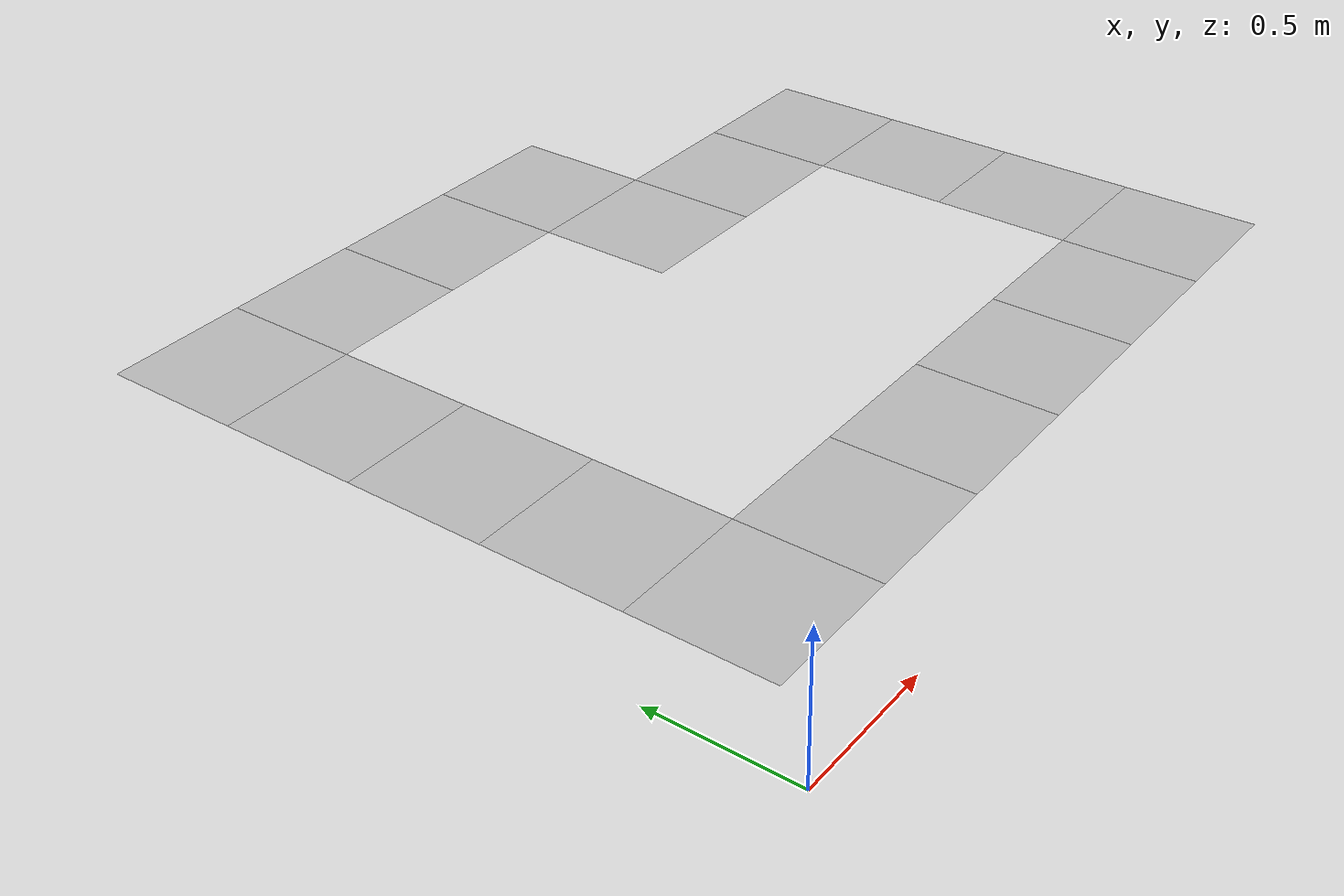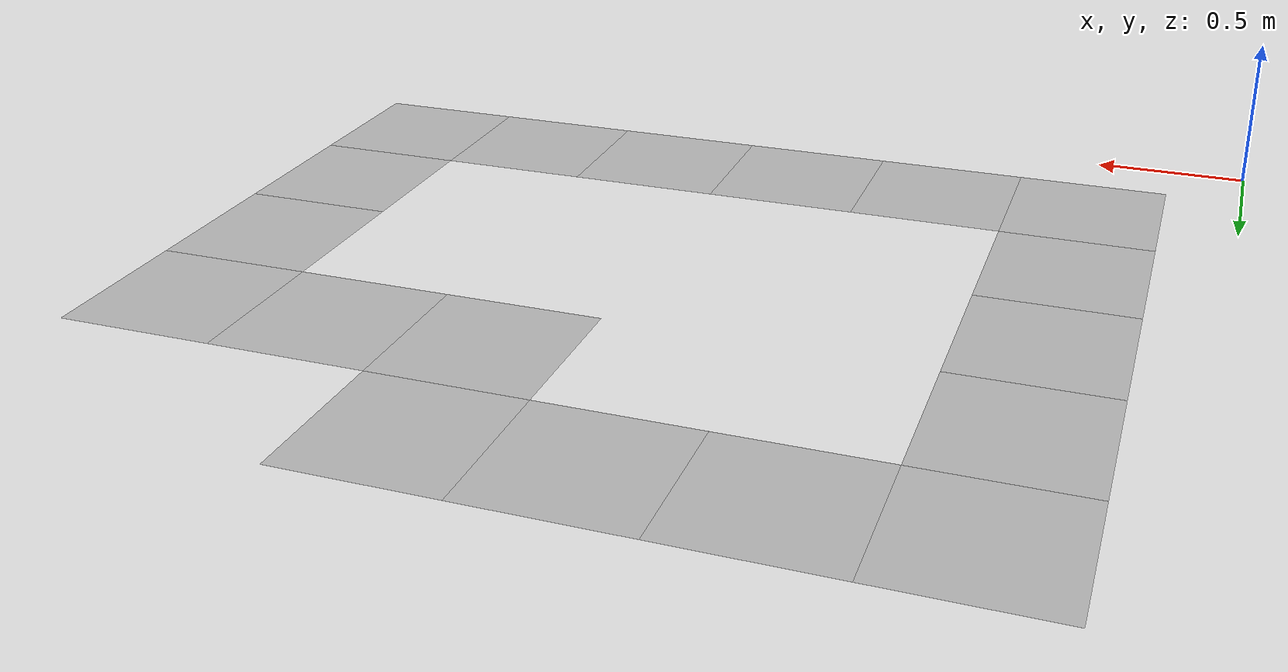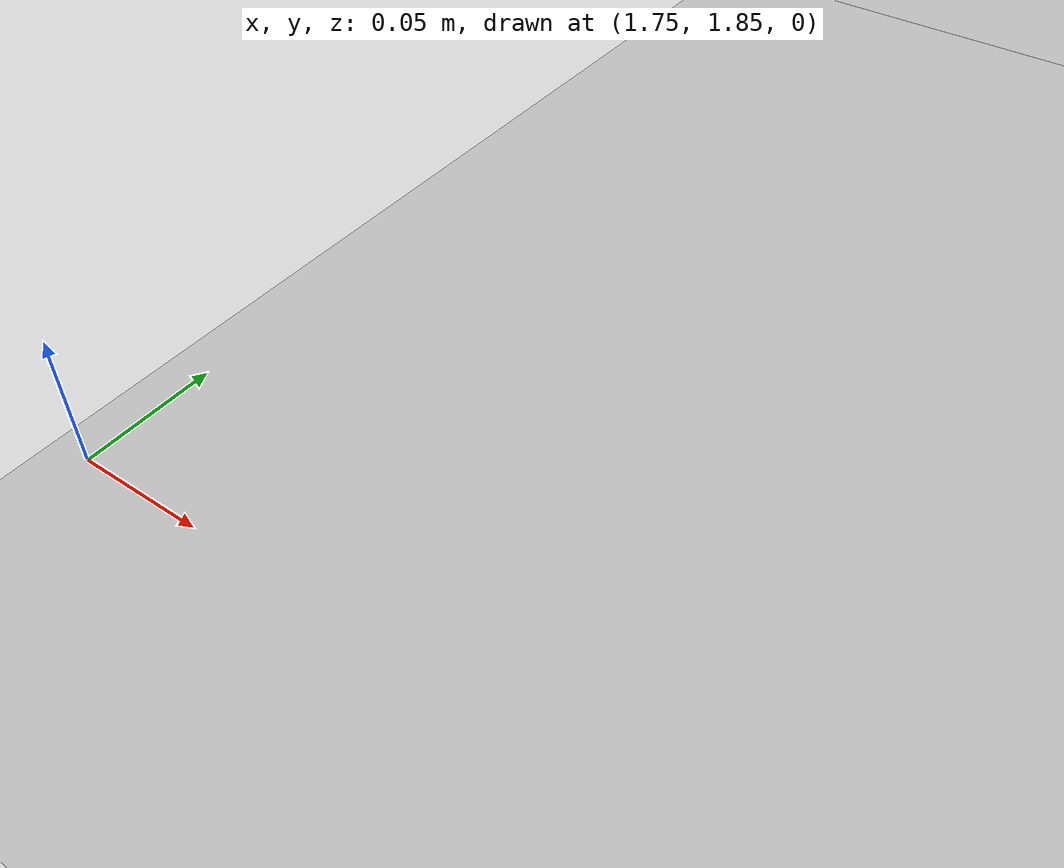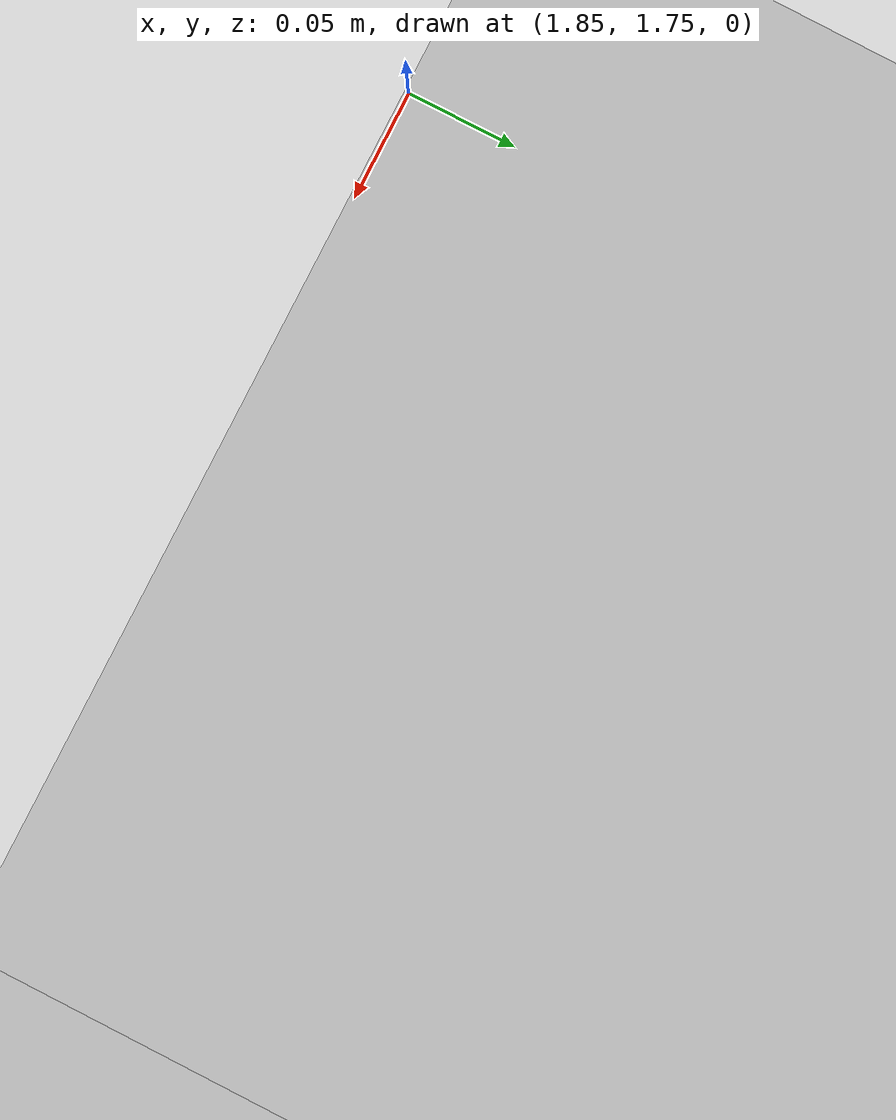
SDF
<sdf version="1.9">
 <world name="default">
  <plugin name="gz::sim::systems::Physics" filename="gz-sim-physics-system"/>
  <plugin name="gz::sim::systems::UserCommands" filename="gz-sim-user-commands-system"/>
  <plugin name="gz::sim::systems::SceneBroadcaster" filename="gz-sim-scene-broadcaster-system"/>
  <plugin name="gz::sim::systems::Sensors" filename="gz-sim-sensors-system">
   <render_engine>ogre2</render_engine>
  </plugin>
  <plugin name="gz::sim::systems::Imu" filename="gz-sim-imu-system"/>
  <gravity>0 0 -9.8</gravity>
  <magnetic_field>6e-06 2.3e-05 -4.2e-05</magnetic_field>
  <atmosphere type="adiabatic"/>
  <physics type="ode">
   <max_step_size>0.001</max_step_size>
   <real_time_factor>1</real_time_factor>
   <real_time_update_rate>1000</real_time_update_rate>
  </physics>
  <scene>
   <ambient>0.4 0.4 0.4 1</ambient>
   <background>0.53 0.81 0.92 1</background>
   <shadows>false</shadows>
  </scene>
  <spherical_coordinates>
   <surface_model>EARTH_WGS84</surface_model>
   <latitude_deg>0</latitude_deg>
   <longitude_deg>0</longitude_deg>
   <elevation>0</elevation>
   <heading_deg>0</heading_deg>
  </spherical_coordinates>
  <plugin name="ignition::gazebo::systems::UserCommands" filename="ignition-gazebo-user-commands-system"/>
  <model name="unit_box_tile_1_1">
   <model name="model_tile_1_1">
    <static>true</static>
    <pose>0.5 0.5 0.01 1.5707963267948966 -0 3.141592653589793</pose>
    <link name="link_tile_1_1">
     <collision name="collision_tile_1_1">
      <geometry>
       <mesh><scale>0.5 0.5 0.5</scale><uri>model://curve_left_1/meshes/curve_left_1.obj</uri></mesh>
      </geometry>
     </collision>
     <visual name="visual_tile_1_1">
      <geometry>
       <mesh>
        <scale>0.5 0.5 0.5</scale>
        <uri>model://curve_left_1/meshes/curve_left_1.obj</uri>
        <pose>0.5 0.5 0.01 1.5707963267948966 -0 3.141592653589793</pose>
       </mesh>
      </geometry>
     </visual>
    </link>
   </model>
   <static>false</static>
  </model>
  <model name="unit_box_tile_2_1">
   <model name="model_tile_2_1">
    <static>true</static>
    <pose>1.0 0.5 0.01 1.5707963267948966 -0 4.71238898038469</pose>
    <link name="link_tile_2_1">
     <collision name="collision_tile_2_1">
      <geometry><mesh><scale>0.5 0.5 0.5</scale><uri>model://straight/meshes/straight.obj</uri></mesh></geometry>
     </collision>
     <visual name="visual_tile_2_1">
      <geometry>
       <mesh>
        <scale>0.5 0.5 0.5</scale>
        <uri>model://straight/meshes/straight.obj</uri>
        <pose>1.0 0.5 0.01 1.5707963267948966 -0 4.71238898038469</pose>
       </mesh>
      </geometry>
     </visual>
    </link>
   </model>
   <static>false</static>
  </model>
  <model name="unit_box_tile_3_1">
   <model name="model_tile_3_1">
    <static>true</static>
    <pose>1.5 0.5 0.01 1.5707963267948966 -0 4.71238898038469</pose>
    <link name="link_tile_3_1">
     <collision name="collision_tile_3_1">
      <geometry><mesh><scale>0.5 0.5 0.5</scale><uri>model://straight/meshes/straight.obj</uri></mesh></geometry>
     </collision>
     <visual name="visual_tile_3_1">
      <geometry>
       <mesh>
        <scale>0.5 0.5 0.5</scale>
        <uri>model://straight/meshes/straight.obj</uri>
        <pose>1.5 0.5 0.01 1.5707963267948966 -0 4.71238898038469</pose>
       </mesh>
      </geometry>
     </visual>
    </link>
   </model>
   <static>false</static>
  </model>
  <model name="unit_box_tile_4_1">
   <model name="model_tile_4_1">
    <static>true</static>
    <pose>2.0 0.5 0.01 1.5707963267948966 -0 4.71238898038469</pose>
    <link name="link_tile_4_1">
     <collision name="collision_tile_4_1">
      <geometry><mesh><scale>0.5 0.5 0.5</scale><uri>model://straight/meshes/straight.obj</uri></mesh></geometry>
     </collision>
     <visual name="visual_tile_4_1">
      <geometry>
       <mesh>
        <scale>0.5 0.5 0.5</scale>
        <uri>model://straight/meshes/straight.obj</uri>
        <pose>2.0 0.5 0.01 1.5707963267948966 -0 4.71238898038469</pose>
       </mesh>
      </geometry>
     </visual>
    </link>
   </model>
   <static>false</static>
  </model>
  <model name="unit_box_tile_5_1">
   <model name="model_tile_5_1">
    <static>true</static>
    <pose>2.5 0.5 0.01 1.5707963267948966 -0 4.71238898038469</pose>
    <link name="link_tile_5_1">
     <collision name="collision_tile_5_1">
      <geometry><mesh><scale>0.5 0.5 0.5</scale><uri>model://straight/meshes/straight.obj</uri></mesh></geometry>
     </collision>
     <visual name="visual_tile_5_1">
      <geometry>
       <mesh>
        <scale>0.5 0.5 0.5</scale>
        <uri>model://straight/meshes/straight.obj</uri>
        <pose>2.5 0.5 0.01 1.5707963267948966 -0 4.71238898038469</pose>
       </mesh>
      </geometry>
     </visual>
    </link>
   </model>
   <static>false</static>
  </model>
  <model name="unit_box_tile_6_1">
   <model name="model_tile_6_1">
    <static>true</static>
    <pose>3.0 0.5 0.01 1.5707963267948966 -0 4.71238898038469</pose>
    <link name="link_tile_6_1">
     <collision name="collision_tile_6_1">
      <geometry>
       <mesh><scale>0.5 0.5 0.5</scale><uri>model://curve_left_1/meshes/curve_left_1.obj</uri></mesh>
      </geometry>
     </collision>
     <visual name="visual_tile_6_1">
      <geometry>
       <mesh>
        <scale>0.5 0.5 0.5</scale>
        <uri>model://curve_left_1/meshes/curve_left_1.obj</uri>
        <pose>3.0 0.5 0.01 1.5707963267948966 -0 4.71238898038469</pose>
       </mesh>
      </geometry>
     </visual>
    </link>
   </model>
   <static>false</static>
  </model>
  <model name="unit_box_tile_1_2">
   <model name="model_tile_1_2">
    <static>true</static>
    <pose>0.5 1.0 0.01 1.5707963267948966 -0 3.141592653589793</pose>
    <link name="link_tile_1_2">
     <collision name="collision_tile_1_2">
      <geometry><mesh><scale>0.5 0.5 0.5</scale><uri>model://straight/meshes/straight.obj</uri></mesh></geometry>
     </collision>
     <visual name="visual_tile_1_2">
      <geometry>
       <mesh>
        <scale>0.5 0.5 0.5</scale>
        <uri>model://straight/meshes/straight.obj</uri>
        <pose>0.5 1.0 0.01 1.5707963267948966 -0 3.141592653589793</pose>
       </mesh>
      </geometry>
     </visual>
    </link>
   </model>
   <static>false</static>
  </model>
  <model name="unit_box_tile_6_2">
   <model name="model_tile_6_2">
    <static>true</static>
    <pose>3.0 1.0 0.01 1.5707963267948966 -0 0.0</pose>
    <link name="link_tile_6_2">
     <collision name="collision_tile_6_2">
      <geometry><mesh><scale>0.5 0.5 0.5</scale><uri>model://straight/meshes/straight.obj</uri></mesh></geometry>
     </collision>
     <visual name="visual_tile_6_2">
      <geometry>
       <mesh>
        <scale>0.5 0.5 0.5</scale>
        <uri>model://straight/meshes/straight.obj</uri>
        <pose>3.0 1.0 0.01 1.5707963267948966 -0 0.0</pose>
       </mesh>
      </geometry>
     </visual>
    </link>
   </model>
   <static>false</static>
  </model>
  <model name="unit_box_tile_1_3">
   <model name="model_tile_1_3">
    <static>true</static>
    <pose>0.5 1.5 0.01 1.5707963267948966 -0 3.141592653589793</pose>
    <link name="link_tile_1_3">
     <collision name="collision_tile_1_3">
      <geometry><mesh><scale>0.5 0.5 0.5</scale><uri>model://straight/meshes/straight.obj</uri></mesh></geometry>
     </collision>
     <visual name="visual_tile_1_3">
      <geometry>
       <mesh>
        <scale>0.5 0.5 0.5</scale>
        <uri>model://straight/meshes/straight.obj</uri>
        <pose>0.5 1.5 0.01 1.5707963267948966 -0 3.141592653589793</pose>
       </mesh>
      </geometry>
     </visual>
    </link>
   </model>
   <static>false</static>
  </model>
  <model name="unit_box_tile_6_3">
   <model name="model_tile_6_3">
    <static>true</static>
    <pose>3.0 1.5 0.01 1.5707963267948966 -0 0.0</pose>
    <link name="link_tile_6_3">
     <collision name="collision_tile_6_3">
      <geometry><mesh><scale>0.5 0.5 0.5</scale><uri>model://straight/meshes/straight.obj</uri></mesh></geometry>
     </collision>
     <visual name="visual_tile_6_3">
      <geometry>
       <mesh>
        <scale>0.5 0.5 0.5</scale>
        <uri>model://straight/meshes/straight.obj</uri>
        <pose>3.0 1.5 0.01 1.5707963267948966 -0 0.0</pose>
       </mesh>
      </geometry>
     </visual>
    </link>
   </model>
   <static>false</static>
  </model>
  <model name="unit_box_tile_1_4">
   <model name="model_tile_1_4">
    <static>true</static>
    <pose>0.5 2.0 0.01 1.5707963267948966 -0 3.141592653589793</pose>
    <link name="link_tile_1_4">
     <collision name="collision_tile_1_4">
      <geometry><mesh><scale>0.5 0.5 0.5</scale><uri>model://straight/meshes/straight.obj</uri></mesh></geometry>
     </collision>
     <visual name="visual_tile_1_4">
      <geometry>
       <mesh>
        <scale>0.5 0.5 0.5</scale>
        <uri>model://straight/meshes/straight.obj</uri>
        <pose>0.5 2.0 0.01 1.5707963267948966 -0 3.141592653589793</pose>
       </mesh>
      </geometry>
     </visual>
    </link>
   </model>
   <static>false</static>
  </model>
  <model name="unit_box_tile_4_4">
   <model name="model_tile_4_4">
    <static>true</static>
    <pose>2.0 2.0 0.01 1.5707963267948966 -0 1.5707963267948966</pose>
    <link name="link_tile_4_4">
     <collision name="collision_tile_4_4">
      <geometry>
       <mesh><scale>0.5 0.5 0.5</scale><uri>model://curve_right_1/meshes/curve_right_1.obj</uri></mesh>
      </geometry>
     </collision>
     <visual name="visual_tile_4_4">
      <geometry>
       <mesh>
        <scale>0.5 0.5 0.5</scale>
        <uri>model://curve_right_1/meshes/curve_right_1.obj</uri>
        <pose>2.0 2.0 0.01 1.5707963267948966 -0 1.5707963267948966</pose>
       </mesh>
      </geometry>
     </visual>
    </link>
   </model>
   <static>false</static>
  </model>
  <model name="unit_box_tile_5_4">
   <model name="model_tile_5_4">
    <static>true</static>
    <pose>2.5 2.0 0.01 1.5707963267948966 -0 1.5707963267948966</pose>
    <link name="link_tile_5_4">
     <collision name="collision_tile_5_4">
      <geometry><mesh><scale>0.5 0.5 0.5</scale><uri>model://straight/meshes/straight.obj</uri></mesh></geometry>
     </collision>
     <visual name="visual_tile_5_4">
      <geometry>
       <mesh>
        <scale>0.5 0.5 0.5</scale>
        <uri>model://straight/meshes/straight.obj</uri>
        <pose>2.5 2.0 0.01 1.5707963267948966 -0 1.5707963267948966</pose>
       </mesh>
      </geometry>
     </visual>
    </link>
   </model>
   <static>false</static>
  </model>
  <model name="unit_box_tile_6_4">
   <model name="model_tile_6_4">
    <static>true</static>
    <pose>3.0 2.0 0.01 1.5707963267948966 -0 0.0</pose>
    <link name="link_tile_6_4">
     <collision name="collision_tile_6_4">
      <geometry>
       <mesh><scale>0.5 0.5 0.5</scale><uri>model://curve_left_1/meshes/curve_left_1.obj</uri></mesh>
      </geometry>
     </collision>
     <visual name="visual_tile_6_4">
      <geometry>
       <mesh>
        <scale>0.5 0.5 0.5</scale>
        <uri>model://curve_left_1/meshes/curve_left_1.obj</uri>
        <pose>3.0 2.0 0.01 1.5707963267948966 -0 0.0</pose>
       </mesh>
      </geometry>
     </visual>
    </link>
   </model>
   <static>false</static>
  </model>
  <model name="unit_box_tile_1_5">
   <model name="model_tile_1_5">
    <static>true</static>
    <pose>0.5 2.5 0.01 1.5707963267948966 -0 1.5707963267948966</pose>
    <link name="link_tile_1_5">
     <collision name="collision_tile_1_5">
      <geometry>
       <mesh><scale>0.5 0.5 0.5</scale><uri>model://curve_left_1/meshes/curve_left_1.obj</uri></mesh>
      </geometry>
     </collision>
     <visual name="visual_tile_1_5">
      <geometry>
       <mesh>
        <scale>0.5 0.5 0.5</scale>
        <uri>model://curve_left_1/meshes/curve_left_1.obj</uri>
        <pose>0.5 2.5 0.01 1.5707963267948966 -0 1.5707963267948966</pose>
       </mesh>
      </geometry>
     </visual>
    </link>
   </model>
   <static>false</static>
  </model>
  <model name="unit_box_tile_2_5">
   <model name="model_tile_2_5">
    <static>true</static>
    <pose>1.0 2.5 0.01 1.5707963267948966 -0 1.5707963267948966</pose>
    <link name="link_tile_2_5">
     <collision name="collision_tile_2_5">
      <geometry><mesh><scale>0.5 0.5 0.5</scale><uri>model://straight/meshes/straight.obj</uri></mesh></geometry>
     </collision>
     <visual name="visual_tile_2_5">
      <geometry>
       <mesh>
        <scale>0.5 0.5 0.5</scale>
        <uri>model://straight/meshes/straight.obj</uri>
        <pose>1.0 2.5 0.01 1.5707963267948966 -0 1.5707963267948966</pose>
       </mesh>
      </geometry>
     </visual>
    </link>
   </model>
   <static>false</static>
  </model>
  <model name="unit_box_tile_3_5">
   <model name="model_tile_3_5">
    <static>true</static>
    <pose>1.5 2.5 0.01 1.5707963267948966 -0 1.5707963267948966</pose>
    <link name="link_tile_3_5">
     <collision name="collision_tile_3_5">
      <geometry><mesh><scale>0.5 0.5 0.5</scale><uri>model://straight/meshes/straight.obj</uri></mesh></geometry>
     </collision>
     <visual name="visual_tile_3_5">
      <geometry>
       <mesh>
        <scale>0.5 0.5 0.5</scale>
        <uri>model://straight/meshes/straight.obj</uri>
        <pose>1.5 2.5 0.01 1.5707963267948966 -0 1.5707963267948966</pose>
       </mesh>
      </geometry>
     </visual>
    </link>
   </model>
   <static>false</static>
  </model>
  <model name="unit_box_tile_4_5">
   <model name="model_tile_4_5">
    <static>true</static>
    <pose>2.0 2.5 0.01 1.5707963267948966 -0 0.0</pose>
    <link name="link_tile_4_5">
     <collision name="collision_tile_4_5">
      <geometry>
       <mesh><scale>0.5 0.5 0.5</scale><uri>model://curve_left_1/meshes/curve_left_1.obj</uri></mesh>
      </geometry>
     </collision>
     <visual name="visual_tile_4_5">
      <geometry>
       <mesh>
        <scale>0.5 0.5 0.5</scale>
        <uri>model://curve_left_1/meshes/curve_left_1.obj</uri>
        <pose>2.0 2.5 0.01 1.5707963267948966 -0 0.0</pose>
       </mesh>
      </geometry>
     </visual>
    </link>
   </model>
   <static>false</static>
  </model>
  <model name="model_obj_0_5_1_5">
   <static>true</static>
   <pose>0.25 0.75 0.01 1.5708 -0 0</pose>
   <link name="link_obj_0_5_1_5">
    <collision name="collision_obj_0_5_1_5">
     <geometry>
      <mesh>
       <scale>0.001586 0.001586 0.001586</scale>
       <uri>file:///home/arendjan/ros2/ros2_rsp/install/mirte_gazebo/share/mirte_gazebo/worlds/model://cone/meshes/cone.obj</uri>
      </mesh>
     </geometry>
    </collision>
    <visual name="visual_obj_0_5_1_5">
     <geometry>
      <mesh>
       <scale>0.001586 0.001586 0.001586</scale>
       <uri>file:///home/arendjan/ros2/ros2_rsp/install/mirte_gazebo/share/mirte_gazebo/worlds/model://cone/meshes/cone.obj</uri>
       <pose>0.25 0.75 0.01 1.5707963267948966 -0 0.0</pose>
      </mesh>
     </geometry>
    </visual>
    <inertial>
     <mass>1</mass>
     <inertia><ixx>1</ixx><ixy>0</ixy><ixz>0</ixz><iyy>1</iyy><iyz>0</iyz><izz>1</izz></inertia>
    </inertial>
   </link>
  </model>
  <model name="model_obj_1_5_0_5">
   <static>true</static>
   <pose>0.75 0.25 0.01 1.5708 -0 0</pose>
   <link name="link_obj_1_5_0_5">
    <collision name="collision_obj_1_5_0_5">
     <geometry>
      <mesh>
       <scale>0.001586 0.001586 0.001586</scale>
       <uri>file:///home/arendjan/ros2/ros2_rsp/install/mirte_gazebo/share/mirte_gazebo/worlds/model://cone/meshes/cone.obj</uri>
      </mesh>
     </geometry>
    </collision>
    <visual name="visual_obj_1_5_0_5">
     <geometry>
      <mesh>
       <scale>0.001586 0.001586 0.001586</scale>
       <uri>file:///home/arendjan/ros2/ros2_rsp/install/mirte_gazebo/share/mirte_gazebo/worlds/model://cone/meshes/cone.obj</uri>
       <pose>0.75 0.25 0.01 1.5707963267948966 -0 0.0</pose>
      </mesh>
     </geometry>
    </visual>
    <inertial>
     <mass>1</mass>
     <inertia><ixx>1</ixx><ixy>0</ixy><ixz>0</ixz><iyy>1</iyy><iyz>0</iyz><izz>1</izz></inertia>
    </inertial>
   </link>
  </model>
  <model name="model_obj_0_55_1_25">
   <static>true</static>
   <pose>0.275 0.625 0.01 1.5708 -0 0</pose>
   <link name="link_obj_0_55_1_25">
    <collision name="collision_obj_0_55_1_25">
     <geometry>
      <mesh>
       <scale>0.001586 0.001586 0.001586</scale>
       <uri>file:///home/arendjan/ros2/ros2_rsp/install/mirte_gazebo/share/mirte_gazebo/worlds/model://cone/meshes/cone.obj</uri>
      </mesh>
     </geometry>
    </collision>
    <visual name="visual_obj_0_55_1_25">
     <geometry>
      <mesh>
       <scale>0.001586 0.001586 0.001586</scale>
       <uri>file:///home/arendjan/ros2/ros2_rsp/install/mirte_gazebo/share/mirte_gazebo/worlds/model://cone/meshes/cone.obj</uri>
       <pose>0.275 0.625 0.01 1.5707963267948966 -0 0.0</pose>
      </mesh>
     </geometry>
    </visual>
    <inertial>
     <mass>1</mass>
     <inertia><ixx>1</ixx><ixy>0</ixy><ixz>0</ixz><iyy>1</iyy><iyz>0</iyz><izz>1</izz></inertia>
    </inertial>
   </link>
  </model>
  <model name="model_obj_1_25_0_55">
   <static>true</static>
   <pose>0.625 0.275 0.01 1.5708 -0 0</pose>
   <link name="link_obj_1_25_0_55">
    <collision name="collision_obj_1_25_0_55">
     <geometry>
      <mesh>
       <scale>0.001586 0.001586 0.001586</scale>
       <uri>file:///home/arendjan/ros2/ros2_rsp/install/mirte_gazebo/share/mirte_gazebo/worlds/model://cone/meshes/cone.obj</uri>
      </mesh>
     </geometry>
    </collision>
    <visual name="visual_obj_1_25_0_55">
     <geometry>
      <mesh>
       <scale>0.001586 0.001586 0.001586</scale>
       <uri>file:///home/arendjan/ros2/ros2_rsp/install/mirte_gazebo/share/mirte_gazebo/worlds/model://cone/meshes/cone.obj</uri>
       <pose>0.625 0.275 0.01 1.5707963267948966 -0 0.0</pose>
      </mesh>
     </geometry>
    </visual>
    <inertial>
     <mass>1</mass>
     <inertia><ixx>1</ixx><ixy>0</ixy><ixz>0</ixz><iyy>1</iyy><iyz>0</iyz><izz>1</izz></inertia>
    </inertial>
   </link>
  </model>
  <model name="model_obj_0_7_0_7">
   <static>true</static>
   <pose>0.35 0.35 0.01 1.5708 -0 0</pose>
   <link name="link_obj_0_7_0_7">
    <collision name="collision_obj_0_7_0_7">
     <geometry>
      <mesh>
       <scale>0.001586 0.001586 0.001586</scale>
       <uri>file:///home/arendjan/ros2/ros2_rsp/install/mirte_gazebo/share/mirte_gazebo/worlds/model://cone/meshes/cone.obj</uri>
      </mesh>
     </geometry>
    </collision>
    <visual name="visual_obj_0_7_0_7">
     <geometry>
      <mesh>
       <scale>0.001586 0.001586 0.001586</scale>
       <uri>file:///home/arendjan/ros2/ros2_rsp/install/mirte_gazebo/share/mirte_gazebo/worlds/model://cone/meshes/cone.obj</uri>
       <pose>0.35 0.35 0.01 1.5707963267948966 -0 0.0</pose>
      </mesh>
     </geometry>
    </visual>
    <inertial>
     <mass>1</mass>
     <inertia><ixx>1</ixx><ixy>0</ixy><ixz>0</ixz><iyy>1</iyy><iyz>0</iyz><izz>1</izz></inertia>
    </inertial>
   </link>
  </model>
  <model name="model_obj_1_0_0_6000000000000001">
   <static>true</static>
   <pose>0.5 0.3 0.01 1.5708 -0 0</pose>
   <link name="link_obj_1_0_0_6000000000000001">
    <collision name="collision_obj_1_0_0_6000000000000001">
     <geometry>
      <mesh>
       <scale>0.001586 0.001586 0.001586</scale>
       <uri>file:///home/arendjan/ros2/ros2_rsp/install/mirte_gazebo/share/mirte_gazebo/worlds/model://cone/meshes/cone.obj</uri>
      </mesh>
     </geometry>
    </collision>
    <visual name="visual_obj_1_0_0_6000000000000001">
     <geometry>
      <mesh>
       <scale>0.001586 0.001586 0.001586</scale>
       <uri>file:///home/arendjan/ros2/ros2_rsp/install/mirte_gazebo/share/mirte_gazebo/worlds/model://cone/meshes/cone.obj</uri>
       <pose>0.5 0.30000000000000004 0.01 1.5707963267948966 -0 0.0</pose>
      </mesh>
     </geometry>
    </visual>
    <inertial>
     <mass>1</mass>
     <inertia><ixx>1</ixx><ixy>0</ixy><ixz>0</ixz><iyy>1</iyy><iyz>0</iyz><izz>1</izz></inertia>
    </inertial>
   </link>
  </model>
  <model name="model_obj_0_6000000000000001_1_0">
   <static>true</static>
   <pose>0.3 0.5 0.01 1.5708 -0 0</pose>
   <link name="link_obj_0_6000000000000001_1_0">
    <collision name="collision_obj_0_6000000000000001_1_0">
     <geometry>
      <mesh>
       <scale>0.001586 0.001586 0.001586</scale>
       <uri>file:///home/arendjan/ros2/ros2_rsp/install/mirte_gazebo/share/mirte_gazebo/worlds/model://cone/meshes/cone.obj</uri>
      </mesh>
     </geometry>
    </collision>
    <visual name="visual_obj_0_6000000000000001_1_0">
     <geometry>
      <mesh>
       <scale>0.001586 0.001586 0.001586</scale>
       <uri>file:///home/arendjan/ros2/ros2_rsp/install/mirte_gazebo/share/mirte_gazebo/worlds/model://cone/meshes/cone.obj</uri>
       <pose>0.30000000000000004 0.5 0.01 1.5707963267948966 -0 0.0</pose>
      </mesh>
     </geometry>
    </visual>
    <inertial>
     <mass>1</mass>
     <inertia><ixx>1</ixx><ixy>0</ixy><ixz>0</ixz><iyy>1</iyy><iyz>0</iyz><izz>1</izz></inertia>
    </inertial>
   </link>
  </model>
  <model name="model_obj_1_75_0_5">
   <static>true</static>
   <pose>0.875 0.25 0.01 1.5708 -0 0</pose>
   <link name="link_obj_1_75_0_5">
    <collision name="collision_obj_1_75_0_5">
     <geometry>
      <mesh>
       <scale>0.001586 0.001586 0.001586</scale>
       <uri>file:///home/arendjan/ros2/ros2_rsp/install/mirte_gazebo/share/mirte_gazebo/worlds/model://cone/meshes/cone.obj</uri>
      </mesh>
     </geometry>
    </collision>
    <visual name="visual_obj_1_75_0_5">
     <geometry>
      <mesh>
       <scale>0.001586 0.001586 0.001586</scale>
       <uri>file:///home/arendjan/ros2/ros2_rsp/install/mirte_gazebo/share/mirte_gazebo/worlds/model://cone/meshes/cone.obj</uri>
       <pose>0.875 0.25 0.01 1.5707963267948966 -0 0.0</pose>
      </mesh>
     </geometry>
    </visual>
    <inertial>
     <mass>1</mass>
     <inertia><ixx>1</ixx><ixy>0</ixy><ixz>0</ixz><iyy>1</iyy><iyz>0</iyz><izz>1</izz></inertia>
    </inertial>
   </link>
  </model>
  <model name="model_obj_2_0_0_5">
   <static>true</static>
   <pose>1 0.25 0.01 1.5708 -0 0</pose>
   <link name="link_obj_2_0_0_5">
    <collision name="collision_obj_2_0_0_5">
     <geometry>
      <mesh>
       <scale>0.001586 0.001586 0.001586</scale>
       <uri>file:///home/arendjan/ros2/ros2_rsp/install/mirte_gazebo/share/mirte_gazebo/worlds/model://cone/meshes/cone.obj</uri>
      </mesh>
     </geometry>
    </collision>
    <visual name="visual_obj_2_0_0_5">
     <geometry>
      <mesh>
       <scale>0.001586 0.001586 0.001586</scale>
       <uri>file:///home/arendjan/ros2/ros2_rsp/install/mirte_gazebo/share/mirte_gazebo/worlds/model://cone/meshes/cone.obj</uri>
       <pose>1.0 0.25 0.01 1.5707963267948966 -0 0.0</pose>
      </mesh>
     </geometry>
    </visual>
    <inertial>
     <mass>1</mass>
     <inertia><ixx>1</ixx><ixy>0</ixy><ixz>0</ixz><iyy>1</iyy><iyz>0</iyz><izz>1</izz></inertia>
    </inertial>
   </link>
  </model>
  <model name="model_obj_2_25_0_5">
   <static>true</static>
   <pose>1.125 0.25 0.01 1.5708 -0 0</pose>
   <link name="link_obj_2_25_0_5">
    <collision name="collision_obj_2_25_0_5">
     <geometry>
      <mesh>
       <scale>0.001586 0.001586 0.001586</scale>
       <uri>file:///home/arendjan/ros2/ros2_rsp/install/mirte_gazebo/share/mirte_gazebo/worlds/model://cone/meshes/cone.obj</uri>
      </mesh>
     </geometry>
    </collision>
    <visual name="visual_obj_2_25_0_5">
     <geometry>
      <mesh>
       <scale>0.001586 0.001586 0.001586</scale>
       <uri>file:///home/arendjan/ros2/ros2_rsp/install/mirte_gazebo/share/mirte_gazebo/worlds/model://cone/meshes/cone.obj</uri>
       <pose>1.125 0.25 0.01 1.5707963267948966 -0 0.0</pose>
      </mesh>
     </geometry>
    </visual>
    <inertial>
     <mass>1</mass>
     <inertia><ixx>1</ixx><ixy>0</ixy><ixz>0</ixz><iyy>1</iyy><iyz>0</iyz><izz>1</izz></inertia>
    </inertial>
   </link>
  </model>
  <model name="model_obj_2_5_0_5">
   <static>true</static>
   <pose>1.25 0.25 0.01 1.5708 -0 0</pose>
   <link name="link_obj_2_5_0_5">
    <collision name="collision_obj_2_5_0_5">
     <geometry>
      <mesh>
       <scale>0.001586 0.001586 0.001586</scale>
       <uri>file:///home/arendjan/ros2/ros2_rsp/install/mirte_gazebo/share/mirte_gazebo/worlds/model://cone/meshes/cone.obj</uri>
      </mesh>
     </geometry>
    </collision>
    <visual name="visual_obj_2_5_0_5">
     <geometry>
      <mesh>
       <scale>0.001586 0.001586 0.001586</scale>
       <uri>file:///home/arendjan/ros2/ros2_rsp/install/mirte_gazebo/share/mirte_gazebo/worlds/model://cone/meshes/cone.obj</uri>
       <pose>1.25 0.25 0.01 1.5707963267948966 -0 0.0</pose>
      </mesh>
     </geometry>
    </visual>
    <inertial>
     <mass>1</mass>
     <inertia><ixx>1</ixx><ixy>0</ixy><ixz>0</ixz><iyy>1</iyy><iyz>0</iyz><izz>1</izz></inertia>
    </inertial>
   </link>
  </model>
  <model name="model_obj_1_5_1_5">
   <static>true</static>
   <pose>0.75 0.75 0.01 1.5708 -0 0</pose>
   <link name="link_obj_1_5_1_5">
    <collision name="collision_obj_1_5_1_5">
     <geometry>
      <mesh>
       <scale>0.001586 0.001586 0.001586</scale>
       <uri>file:///home/arendjan/ros2/ros2_rsp/install/mirte_gazebo/share/mirte_gazebo/worlds/model://cone/meshes/cone.obj</uri>
      </mesh>
     </geometry>
    </collision>
    <visual name="visual_obj_1_5_1_5">
     <geometry>
      <mesh>
       <scale>0.001586 0.001586 0.001586</scale>
       <uri>file:///home/arendjan/ros2/ros2_rsp/install/mirte_gazebo/share/mirte_gazebo/worlds/model://cone/meshes/cone.obj</uri>
       <pose>0.75 0.75 0.01 1.5707963267948966 -0 0.0</pose>
      </mesh>
     </geometry>
    </visual>
    <inertial>
     <mass>1</mass>
     <inertia><ixx>1</ixx><ixy>0</ixy><ixz>0</ixz><iyy>1</iyy><iyz>0</iyz><izz>1</izz></inertia>
    </inertial>
   </link>
  </model>
  <model name="model_obj_1_75_1_5">
   <static>true</static>
   <pose>0.875 0.75 0.01 1.5708 -0 0</pose>
   <link name="link_obj_1_75_1_5">
    <collision name="collision_obj_1_75_1_5">
     <geometry>
      <mesh>
       <scale>0.001586 0.001586 0.001586</scale>
       <uri>file:///home/arendjan/ros2/ros2_rsp/install/mirte_gazebo/share/mirte_gazebo/worlds/model://cone/meshes/cone.obj</uri>
      </mesh>
     </geometry>
    </collision>
    <visual name="visual_obj_1_75_1_5">
     <geometry>
      <mesh>
       <scale>0.001586 0.001586 0.001586</scale>
       <uri>file:///home/arendjan/ros2/ros2_rsp/install/mirte_gazebo/share/mirte_gazebo/worlds/model://cone/meshes/cone.obj</uri>
       <pose>0.875 0.75 0.01 1.5707963267948966 -0 0.0</pose>
      </mesh>
     </geometry>
    </visual>
    <inertial>
     <mass>1</mass>
     <inertia><ixx>1</ixx><ixy>0</ixy><ixz>0</ixz><iyy>1</iyy><iyz>0</iyz><izz>1</izz></inertia>
    </inertial>
   </link>
  </model>
  <model name="model_obj_2_0_1_5">
   <static>true</static>
   <pose>1 0.75 0.01 1.5708 -0 0</pose>
   <link name="link_obj_2_0_1_5">
    <collision name="collision_obj_2_0_1_5">
     <geometry>
      <mesh>
       <scale>0.001586 0.001586 0.001586</scale>
       <uri>file:///home/arendjan/ros2/ros2_rsp/install/mirte_gazebo/share/mirte_gazebo/worlds/model://cone/meshes/cone.obj</uri>
      </mesh>
     </geometry>
    </collision>
    <visual name="visual_obj_2_0_1_5">
     <geometry>
      <mesh>
       <scale>0.001586 0.001586 0.001586</scale>
       <uri>file:///home/arendjan/ros2/ros2_rsp/install/mirte_gazebo/share/mirte_gazebo/worlds/model://cone/meshes/cone.obj</uri>
       <pose>1.0 0.75 0.01 1.5707963267948966 -0 0.0</pose>
      </mesh>
     </geometry>
    </visual>
    <inertial>
     <mass>1</mass>
     <inertia><ixx>1</ixx><ixy>0</ixy><ixz>0</ixz><iyy>1</iyy><iyz>0</iyz><izz>1</izz></inertia>
    </inertial>
   </link>
  </model>
  <model name="model_obj_2_25_1_5">
   <static>true</static>
   <pose>1.125 0.75 0.01 1.5708 -0 0</pose>
   <link name="link_obj_2_25_1_5">
    <collision name="collision_obj_2_25_1_5">
     <geometry>
      <mesh>
       <scale>0.001586 0.001586 0.001586</scale>
       <uri>file:///home/arendjan/ros2/ros2_rsp/install/mirte_gazebo/share/mirte_gazebo/worlds/model://cone/meshes/cone.obj</uri>
      </mesh>
     </geometry>
    </collision>
    <visual name="visual_obj_2_25_1_5">
     <geometry>
      <mesh>
       <scale>0.001586 0.001586 0.001586</scale>
       <uri>file:///home/arendjan/ros2/ros2_rsp/install/mirte_gazebo/share/mirte_gazebo/worlds/model://cone/meshes/cone.obj</uri>
       <pose>1.125 0.75 0.01 1.5707963267948966 -0 0.0</pose>
      </mesh>
     </geometry>
    </visual>
    <inertial>
     <mass>1</mass>
     <inertia><ixx>1</ixx><ixy>0</ixy><ixz>0</ixz><iyy>1</iyy><iyz>0</iyz><izz>1</izz></inertia>
    </inertial>
   </link>
  </model>
  <model name="model_obj_2_5_1_5">
   <static>true</static>
   <pose>1.25 0.75 0.01 1.5708 -0 0</pose>
   <link name="link_obj_2_5_1_5">
    <collision name="collision_obj_2_5_1_5">
     <geometry>
      <mesh>
       <scale>0.001586 0.001586 0.001586</scale>
       <uri>file:///home/arendjan/ros2/ros2_rsp/install/mirte_gazebo/share/mirte_gazebo/worlds/model://cone/meshes/cone.obj</uri>
      </mesh>
     </geometry>
    </collision>
    <visual name="visual_obj_2_5_1_5">
     <geometry>
      <mesh>
       <scale>0.001586 0.001586 0.001586</scale>
       <uri>file:///home/arendjan/ros2/ros2_rsp/install/mirte_gazebo/share/mirte_gazebo/worlds/model://cone/meshes/cone.obj</uri>
       <pose>1.25 0.75 0.01 1.5707963267948966 -0 0.0</pose>
      </mesh>
     </geometry>
    </visual>
    <inertial>
     <mass>1</mass>
     <inertia><ixx>1</ixx><ixy>0</ixy><ixz>0</ixz><iyy>1</iyy><iyz>0</iyz><izz>1</izz></inertia>
    </inertial>
   </link>
  </model>
  <model name="model_obj_2_75_0_5">
   <static>true</static>
   <pose>1.375 0.25 0.01 1.5708 -0 0</pose>
   <link name="link_obj_2_75_0_5">
    <collision name="collision_obj_2_75_0_5">
     <geometry>
      <mesh>
       <scale>0.001586 0.001586 0.001586</scale>
       <uri>file:///home/arendjan/ros2/ros2_rsp/install/mirte_gazebo/share/mirte_gazebo/worlds/model://cone/meshes/cone.obj</uri>
      </mesh>
     </geometry>
    </collision>
    <visual name="visual_obj_2_75_0_5">
     <geometry>
      <mesh>
       <scale>0.001586 0.001586 0.001586</scale>
       <uri>file:///home/arendjan/ros2/ros2_rsp/install/mirte_gazebo/share/mirte_gazebo/worlds/model://cone/meshes/cone.obj</uri>
       <pose>1.375 0.25 0.01 1.5707963267948966 -0 0.0</pose>
      </mesh>
     </geometry>
    </visual>
    <inertial>
     <mass>1</mass>
     <inertia><ixx>1</ixx><ixy>0</ixy><ixz>0</ixz><iyy>1</iyy><iyz>0</iyz><izz>1</izz></inertia>
    </inertial>
   </link>
  </model>
  <model name="model_obj_3_0_0_5">
   <static>true</static>
   <pose>1.5 0.25 0.01 1.5708 -0 0</pose>
   <link name="link_obj_3_0_0_5">
    <collision name="collision_obj_3_0_0_5">
     <geometry>
      <mesh>
       <scale>0.001586 0.001586 0.001586</scale>
       <uri>file:///home/arendjan/ros2/ros2_rsp/install/mirte_gazebo/share/mirte_gazebo/worlds/model://cone/meshes/cone.obj</uri>
      </mesh>
     </geometry>
    </collision>
    <visual name="visual_obj_3_0_0_5">
     <geometry>
      <mesh>
       <scale>0.001586 0.001586 0.001586</scale>
       <uri>file:///home/arendjan/ros2/ros2_rsp/install/mirte_gazebo/share/mirte_gazebo/worlds/model://cone/meshes/cone.obj</uri>
       <pose>1.5 0.25 0.01 1.5707963267948966 -0 0.0</pose>
      </mesh>
     </geometry>
    </visual>
    <inertial>
     <mass>1</mass>
     <inertia><ixx>1</ixx><ixy>0</ixy><ixz>0</ixz><iyy>1</iyy><iyz>0</iyz><izz>1</izz></inertia>
    </inertial>
   </link>
  </model>
  <model name="model_obj_3_25_0_5">
   <static>true</static>
   <pose>1.625 0.25 0.01 1.5708 -0 0</pose>
   <link name="link_obj_3_25_0_5">
    <collision name="collision_obj_3_25_0_5">
     <geometry>
      <mesh>
       <scale>0.001586 0.001586 0.001586</scale>
       <uri>file:///home/arendjan/ros2/ros2_rsp/install/mirte_gazebo/share/mirte_gazebo/worlds/model://cone/meshes/cone.obj</uri>
      </mesh>
     </geometry>
    </collision>
    <visual name="visual_obj_3_25_0_5">
     <geometry>
      <mesh>
       <scale>0.001586 0.001586 0.001586</scale>
       <uri>file:///home/arendjan/ros2/ros2_rsp/install/mirte_gazebo/share/mirte_gazebo/worlds/model://cone/meshes/cone.obj</uri>
       <pose>1.625 0.25 0.01 1.5707963267948966 -0 0.0</pose>
      </mesh>
     </geometry>
    </visual>
    <inertial>
     <mass>1</mass>
     <inertia><ixx>1</ixx><ixy>0</ixy><ixz>0</ixz><iyy>1</iyy><iyz>0</iyz><izz>1</izz></inertia>
    </inertial>
   </link>
  </model>
  <model name="model_obj_3_5_0_5">
   <static>true</static>
   <pose>1.75 0.25 0.01 1.5708 -0 0</pose>
   <link name="link_obj_3_5_0_5">
    <collision name="collision_obj_3_5_0_5">
     <geometry>
      <mesh>
       <scale>0.001586 0.001586 0.001586</scale>
       <uri>file:///home/arendjan/ros2/ros2_rsp/install/mirte_gazebo/share/mirte_gazebo/worlds/model://cone/meshes/cone.obj</uri>
      </mesh>
     </geometry>
    </collision>
    <visual name="visual_obj_3_5_0_5">
     <geometry>
      <mesh>
       <scale>0.001586 0.001586 0.001586</scale>
       <uri>file:///home/arendjan/ros2/ros2_rsp/install/mirte_gazebo/share/mirte_gazebo/worlds/model://cone/meshes/cone.obj</uri>
       <pose>1.75 0.25 0.01 1.5707963267948966 -0 0.0</pose>
      </mesh>
     </geometry>
    </visual>
    <inertial>
     <mass>1</mass>
     <inertia><ixx>1</ixx><ixy>0</ixy><ixz>0</ixz><iyy>1</iyy><iyz>0</iyz><izz>1</izz></inertia>
    </inertial>
   </link>
  </model>
  <model name="model_obj_2_75_1_5">
   <static>true</static>
   <pose>1.375 0.75 0.01 1.5708 -0 0</pose>
   <link name="link_obj_2_75_1_5">
    <collision name="collision_obj_2_75_1_5">
     <geometry>
      <mesh>
       <scale>0.001586 0.001586 0.001586</scale>
       <uri>file:///home/arendjan/ros2/ros2_rsp/install/mirte_gazebo/share/mirte_gazebo/worlds/model://cone/meshes/cone.obj</uri>
      </mesh>
     </geometry>
    </collision>
    <visual name="visual_obj_2_75_1_5">
     <geometry>
      <mesh>
       <scale>0.001586 0.001586 0.001586</scale>
       <uri>file:///home/arendjan/ros2/ros2_rsp/install/mirte_gazebo/share/mirte_gazebo/worlds/model://cone/meshes/cone.obj</uri>
       <pose>1.375 0.75 0.01 1.5707963267948966 -0 0.0</pose>
      </mesh>
     </geometry>
    </visual>
    <inertial>
     <mass>1</mass>
     <inertia><ixx>1</ixx><ixy>0</ixy><ixz>0</ixz><iyy>1</iyy><iyz>0</iyz><izz>1</izz></inertia>
    </inertial>
   </link>
  </model>
  <model name="model_obj_3_0_1_5">
   <static>true</static>
   <pose>1.5 0.75 0.01 1.5708 -0 0</pose>
   <link name="link_obj_3_0_1_5">
    <collision name="collision_obj_3_0_1_5">
     <geometry>
      <mesh>
       <scale>0.001586 0.001586 0.001586</scale>
       <uri>file:///home/arendjan/ros2/ros2_rsp/install/mirte_gazebo/share/mirte_gazebo/worlds/model://cone/meshes/cone.obj</uri>
      </mesh>
     </geometry>
    </collision>
    <visual name="visual_obj_3_0_1_5">
     <geometry>
      <mesh>
       <scale>0.001586 0.001586 0.001586</scale>
       <uri>file:///home/arendjan/ros2/ros2_rsp/install/mirte_gazebo/share/mirte_gazebo/worlds/model://cone/meshes/cone.obj</uri>
       <pose>1.5 0.75 0.01 1.5707963267948966 -0 0.0</pose>
      </mesh>
     </geometry>
    </visual>
    <inertial>
     <mass>1</mass>
     <inertia><ixx>1</ixx><ixy>0</ixy><ixz>0</ixz><iyy>1</iyy><iyz>0</iyz><izz>1</izz></inertia>
    </inertial>
   </link>
  </model>
  <model name="model_obj_3_25_1_5">
   <static>true</static>
   <pose>1.625 0.75 0.01 1.5708 -0 0</pose>
   <link name="link_obj_3_25_1_5">
    <collision name="collision_obj_3_25_1_5">
     <geometry>
      <mesh>
       <scale>0.001586 0.001586 0.001586</scale>
       <uri>file:///home/arendjan/ros2/ros2_rsp/install/mirte_gazebo/share/mirte_gazebo/worlds/model://cone/meshes/cone.obj</uri>
      </mesh>
     </geometry>
    </collision>
    <visual name="visual_obj_3_25_1_5">
     <geometry>
      <mesh>
       <scale>0.001586 0.001586 0.001586</scale>
       <uri>file:///home/arendjan/ros2/ros2_rsp/install/mirte_gazebo/share/mirte_gazebo/worlds/model://cone/meshes/cone.obj</uri>
       <pose>1.625 0.75 0.01 1.5707963267948966 -0 0.0</pose>
      </mesh>
     </geometry>
    </visual>
    <inertial>
     <mass>1</mass>
     <inertia><ixx>1</ixx><ixy>0</ixy><ixz>0</ixz><iyy>1</iyy><iyz>0</iyz><izz>1</izz></inertia>
    </inertial>
   </link>
  </model>
  <model name="model_obj_3_5_1_5">
   <static>true</static>
   <pose>1.75 0.75 0.01 1.5708 -0 0</pose>
   <link name="link_obj_3_5_1_5">
    <collision name="collision_obj_3_5_1_5">
     <geometry>
      <mesh>
       <scale>0.001586 0.001586 0.001586</scale>
       <uri>file:///home/arendjan/ros2/ros2_rsp/install/mirte_gazebo/share/mirte_gazebo/worlds/model://cone/meshes/cone.obj</uri>
      </mesh>
     </geometry>
    </collision>
    <visual name="visual_obj_3_5_1_5">
     <geometry>
      <mesh>
       <scale>0.001586 0.001586 0.001586</scale>
       <uri>file:///home/arendjan/ros2/ros2_rsp/install/mirte_gazebo/share/mirte_gazebo/worlds/model://cone/meshes/cone.obj</uri>
       <pose>1.75 0.75 0.01 1.5707963267948966 -0 0.0</pose>
      </mesh>
     </geometry>
    </visual>
    <inertial>
     <mass>1</mass>
     <inertia><ixx>1</ixx><ixy>0</ixy><ixz>0</ixz><iyy>1</iyy><iyz>0</iyz><izz>1</izz></inertia>
    </inertial>
   </link>
  </model>
  <model name="model_obj_3_75_0_5">
   <static>true</static>
   <pose>1.875 0.25 0.01 1.5708 -0 0</pose>
   <link name="link_obj_3_75_0_5">
    <collision name="collision_obj_3_75_0_5">
     <geometry>
      <mesh>
       <scale>0.001586 0.001586 0.001586</scale>
       <uri>file:///home/arendjan/ros2/ros2_rsp/install/mirte_gazebo/share/mirte_gazebo/worlds/model://cone/meshes/cone.obj</uri>
      </mesh>
     </geometry>
    </collision>
    <visual name="visual_obj_3_75_0_5">
     <geometry>
      <mesh>
       <scale>0.001586 0.001586 0.001586</scale>
       <uri>file:///home/arendjan/ros2/ros2_rsp/install/mirte_gazebo/share/mirte_gazebo/worlds/model://cone/meshes/cone.obj</uri>
       <pose>1.875 0.25 0.01 1.5707963267948966 -0 0.0</pose>
      </mesh>
     </geometry>
    </visual>
    <inertial>
     <mass>1</mass>
     <inertia><ixx>1</ixx><ixy>0</ixy><ixz>0</ixz><iyy>1</iyy><iyz>0</iyz><izz>1</izz></inertia>
    </inertial>
   </link>
  </model>
  <model name="model_obj_4_0_0_5">
   <static>true</static>
   <pose>2 0.25 0.01 1.5708 -0 0</pose>
   <link name="link_obj_4_0_0_5">
    <collision name="collision_obj_4_0_0_5">
     <geometry>
      <mesh>
       <scale>0.001586 0.001586 0.001586</scale>
       <uri>file:///home/arendjan/ros2/ros2_rsp/install/mirte_gazebo/share/mirte_gazebo/worlds/model://cone/meshes/cone.obj</uri>
      </mesh>
     </geometry>
    </collision>
    <visual name="visual_obj_4_0_0_5">
     <geometry>
      <mesh>
       <scale>0.001586 0.001586 0.001586</scale>
       <uri>file:///home/arendjan/ros2/ros2_rsp/install/mirte_gazebo/share/mirte_gazebo/worlds/model://cone/meshes/cone.obj</uri>
       <pose>2.0 0.25 0.01 1.5707963267948966 -0 0.0</pose>
      </mesh>
     </geometry>
    </visual>
    <inertial>
     <mass>1</mass>
     <inertia><ixx>1</ixx><ixy>0</ixy><ixz>0</ixz><iyy>1</iyy><iyz>0</iyz><izz>1</izz></inertia>
    </inertial>
   </link>
  </model>
  <model name="model_obj_4_25_0_5">
   <static>true</static>
   <pose>2.125 0.25 0.01 1.5708 -0 0</pose>
   <link name="link_obj_4_25_0_5">
    <collision name="collision_obj_4_25_0_5">
     <geometry>
      <mesh>
       <scale>0.001586 0.001586 0.001586</scale>
       <uri>file:///home/arendjan/ros2/ros2_rsp/install/mirte_gazebo/share/mirte_gazebo/worlds/model://cone/meshes/cone.obj</uri>
      </mesh>
     </geometry>
    </collision>
    <visual name="visual_obj_4_25_0_5">
     <geometry>
      <mesh>
       <scale>0.001586 0.001586 0.001586</scale>
       <uri>file:///home/arendjan/ros2/ros2_rsp/install/mirte_gazebo/share/mirte_gazebo/worlds/model://cone/meshes/cone.obj</uri>
       <pose>2.125 0.25 0.01 1.5707963267948966 -0 0.0</pose>
      </mesh>
     </geometry>
    </visual>
    <inertial>
     <mass>1</mass>
     <inertia><ixx>1</ixx><ixy>0</ixy><ixz>0</ixz><iyy>1</iyy><iyz>0</iyz><izz>1</izz></inertia>
    </inertial>
   </link>
  </model>
  <model name="model_obj_4_5_0_5">
   <static>true</static>
   <pose>2.25 0.25 0.01 1.5708 -0 0</pose>
   <link name="link_obj_4_5_0_5">
    <collision name="collision_obj_4_5_0_5">
     <geometry>
      <mesh>
       <scale>0.001586 0.001586 0.001586</scale>
       <uri>file:///home/arendjan/ros2/ros2_rsp/install/mirte_gazebo/share/mirte_gazebo/worlds/model://cone/meshes/cone.obj</uri>
      </mesh>
     </geometry>
    </collision>
    <visual name="visual_obj_4_5_0_5">
     <geometry>
      <mesh>
       <scale>0.001586 0.001586 0.001586</scale>
       <uri>file:///home/arendjan/ros2/ros2_rsp/install/mirte_gazebo/share/mirte_gazebo/worlds/model://cone/meshes/cone.obj</uri>
       <pose>2.25 0.25 0.01 1.5707963267948966 -0 0.0</pose>
      </mesh>
     </geometry>
    </visual>
    <inertial>
     <mass>1</mass>
     <inertia><ixx>1</ixx><ixy>0</ixy><ixz>0</ixz><iyy>1</iyy><iyz>0</iyz><izz>1</izz></inertia>
    </inertial>
   </link>
  </model>
  <model name="model_obj_3_75_1_5">
   <static>true</static>
   <pose>1.875 0.75 0.01 1.5708 -0 0</pose>
   <link name="link_obj_3_75_1_5">
    <collision name="collision_obj_3_75_1_5">
     <geometry>
      <mesh>
       <scale>0.001586 0.001586 0.001586</scale>
       <uri>file:///home/arendjan/ros2/ros2_rsp/install/mirte_gazebo/share/mirte_gazebo/worlds/model://cone/meshes/cone.obj</uri>
      </mesh>
     </geometry>
    </collision>
    <visual name="visual_obj_3_75_1_5">
     <geometry>
      <mesh>
       <scale>0.001586 0.001586 0.001586</scale>
       <uri>file:///home/arendjan/ros2/ros2_rsp/install/mirte_gazebo/share/mirte_gazebo/worlds/model://cone/meshes/cone.obj</uri>
       <pose>1.875 0.75 0.01 1.5707963267948966 -0 0.0</pose>
      </mesh>
     </geometry>
    </visual>
    <inertial>
     <mass>1</mass>
     <inertia><ixx>1</ixx><ixy>0</ixy><ixz>0</ixz><iyy>1</iyy><iyz>0</iyz><izz>1</izz></inertia>
    </inertial>
   </link>
  </model>
  <model name="model_obj_4_0_1_5">
   <static>true</static>
   <pose>2 0.75 0.01 1.5708 -0 0</pose>
   <link name="link_obj_4_0_1_5">
    <collision name="collision_obj_4_0_1_5">
     <geometry>
      <mesh>
       <scale>0.001586 0.001586 0.001586</scale>
       <uri>file:///home/arendjan/ros2/ros2_rsp/install/mirte_gazebo/share/mirte_gazebo/worlds/model://cone/meshes/cone.obj</uri>
      </mesh>
     </geometry>
    </collision>
    <visual name="visual_obj_4_0_1_5">
     <geometry>
      <mesh>
       <scale>0.001586 0.001586 0.001586</scale>
       <uri>file:///home/arendjan/ros2/ros2_rsp/install/mirte_gazebo/share/mirte_gazebo/worlds/model://cone/meshes/cone.obj</uri>
       <pose>2.0 0.75 0.01 1.5707963267948966 -0 0.0</pose>
      </mesh>
     </geometry>
    </visual>
    <inertial>
     <mass>1</mass>
     <inertia><ixx>1</ixx><ixy>0</ixy><ixz>0</ixz><iyy>1</iyy><iyz>0</iyz><izz>1</izz></inertia>
    </inertial>
   </link>
  </model>
  <model name="model_obj_4_25_1_5">
   <static>true</static>
   <pose>2.125 0.75 0.01 1.5708 -0 0</pose>
   <link name="link_obj_4_25_1_5">
    <collision name="collision_obj_4_25_1_5">
     <geometry>
      <mesh>
       <scale>0.001586 0.001586 0.001586</scale>
       <uri>file:///home/arendjan/ros2/ros2_rsp/install/mirte_gazebo/share/mirte_gazebo/worlds/model://cone/meshes/cone.obj</uri>
      </mesh>
     </geometry>
    </collision>
    <visual name="visual_obj_4_25_1_5">
     <geometry>
      <mesh>
       <scale>0.001586 0.001586 0.001586</scale>
       <uri>file:///home/arendjan/ros2/ros2_rsp/install/mirte_gazebo/share/mirte_gazebo/worlds/model://cone/meshes/cone.obj</uri>
       <pose>2.125 0.75 0.01 1.5707963267948966 -0 0.0</pose>
      </mesh>
     </geometry>
    </visual>
    <inertial>
     <mass>1</mass>
     <inertia><ixx>1</ixx><ixy>0</ixy><ixz>0</ixz><iyy>1</iyy><iyz>0</iyz><izz>1</izz></inertia>
    </inertial>
   </link>
  </model>
  <model name="model_obj_4_5_1_5">
   <static>true</static>
   <pose>2.25 0.75 0.01 1.5708 -0 0</pose>
   <link name="link_obj_4_5_1_5">
    <collision name="collision_obj_4_5_1_5">
     <geometry>
      <mesh>
       <scale>0.001586 0.001586 0.001586</scale>
       <uri>file:///home/arendjan/ros2/ros2_rsp/install/mirte_gazebo/share/mirte_gazebo/worlds/model://cone/meshes/cone.obj</uri>
      </mesh>
     </geometry>
    </collision>
    <visual name="visual_obj_4_5_1_5">
     <geometry>
      <mesh>
       <scale>0.001586 0.001586 0.001586</scale>
       <uri>file:///home/arendjan/ros2/ros2_rsp/install/mirte_gazebo/share/mirte_gazebo/worlds/model://cone/meshes/cone.obj</uri>
       <pose>2.25 0.75 0.01 1.5707963267948966 -0 0.0</pose>
      </mesh>
     </geometry>
    </visual>
    <inertial>
     <mass>1</mass>
     <inertia><ixx>1</ixx><ixy>0</ixy><ixz>0</ixz><iyy>1</iyy><iyz>0</iyz><izz>1</izz></inertia>
    </inertial>
   </link>
  </model>
  <model name="model_obj_4_75_0_5">
   <static>true</static>
   <pose>2.375 0.25 0.01 1.5708 -0 0</pose>
   <link name="link_obj_4_75_0_5">
    <collision name="collision_obj_4_75_0_5">
     <geometry>
      <mesh>
       <scale>0.001586 0.001586 0.001586</scale>
       <uri>file:///home/arendjan/ros2/ros2_rsp/install/mirte_gazebo/share/mirte_gazebo/worlds/model://cone/meshes/cone.obj</uri>
      </mesh>
     </geometry>
    </collision>
    <visual name="visual_obj_4_75_0_5">
     <geometry>
      <mesh>
       <scale>0.001586 0.001586 0.001586</scale>
       <uri>file:///home/arendjan/ros2/ros2_rsp/install/mirte_gazebo/share/mirte_gazebo/worlds/model://cone/meshes/cone.obj</uri>
       <pose>2.375 0.25 0.01 1.5707963267948966 -0 0.0</pose>
      </mesh>
     </geometry>
    </visual>
    <inertial>
     <mass>1</mass>
     <inertia><ixx>1</ixx><ixy>0</ixy><ixz>0</ixz><iyy>1</iyy><iyz>0</iyz><izz>1</izz></inertia>
    </inertial>
   </link>
  </model>
  <model name="model_obj_5_0_0_5">
   <static>true</static>
   <pose>2.5 0.25 0.01 1.5708 -0 0</pose>
   <link name="link_obj_5_0_0_5">
    <collision name="collision_obj_5_0_0_5">
     <geometry>
      <mesh>
       <scale>0.001586 0.001586 0.001586</scale>
       <uri>file:///home/arendjan/ros2/ros2_rsp/install/mirte_gazebo/share/mirte_gazebo/worlds/model://cone/meshes/cone.obj</uri>
      </mesh>
     </geometry>
    </collision>
    <visual name="visual_obj_5_0_0_5">
     <geometry>
      <mesh>
       <scale>0.001586 0.001586 0.001586</scale>
       <uri>file:///home/arendjan/ros2/ros2_rsp/install/mirte_gazebo/share/mirte_gazebo/worlds/model://cone/meshes/cone.obj</uri>
       <pose>2.5 0.25 0.01 1.5707963267948966 -0 0.0</pose>
      </mesh>
     </geometry>
    </visual>
    <inertial>
     <mass>1</mass>
     <inertia><ixx>1</ixx><ixy>0</ixy><ixz>0</ixz><iyy>1</iyy><iyz>0</iyz><izz>1</izz></inertia>
    </inertial>
   </link>
  </model>
  <model name="model_obj_5_25_0_5">
   <static>true</static>
   <pose>2.625 0.25 0.01 1.5708 -0 0</pose>
   <link name="link_obj_5_25_0_5">
    <collision name="collision_obj_5_25_0_5">
     <geometry>
      <mesh>
       <scale>0.001586 0.001586 0.001586</scale>
       <uri>file:///home/arendjan/ros2/ros2_rsp/install/mirte_gazebo/share/mirte_gazebo/worlds/model://cone/meshes/cone.obj</uri>
      </mesh>
     </geometry>
    </collision>
    <visual name="visual_obj_5_25_0_5">
     <geometry>
      <mesh>
       <scale>0.001586 0.001586 0.001586</scale>
       <uri>file:///home/arendjan/ros2/ros2_rsp/install/mirte_gazebo/share/mirte_gazebo/worlds/model://cone/meshes/cone.obj</uri>
       <pose>2.625 0.25 0.01 1.5707963267948966 -0 0.0</pose>
      </mesh>
     </geometry>
    </visual>
    <inertial>
     <mass>1</mass>
     <inertia><ixx>1</ixx><ixy>0</ixy><ixz>0</ixz><iyy>1</iyy><iyz>0</iyz><izz>1</izz></inertia>
    </inertial>
   </link>
  </model>
  <model name="model_obj_5_5_0_5">
   <static>true</static>
   <pose>2.75 0.25 0.01 1.5708 -0 0</pose>
   <link name="link_obj_5_5_0_5">
    <collision name="collision_obj_5_5_0_5">
     <geometry>
      <mesh>
       <scale>0.001586 0.001586 0.001586</scale>
       <uri>file:///home/arendjan/ros2/ros2_rsp/install/mirte_gazebo/share/mirte_gazebo/worlds/model://cone/meshes/cone.obj</uri>
      </mesh>
     </geometry>
    </collision>
    <visual name="visual_obj_5_5_0_5">
     <geometry>
      <mesh>
       <scale>0.001586 0.001586 0.001586</scale>
       <uri>file:///home/arendjan/ros2/ros2_rsp/install/mirte_gazebo/share/mirte_gazebo/worlds/model://cone/meshes/cone.obj</uri>
       <pose>2.75 0.25 0.01 1.5707963267948966 -0 0.0</pose>
      </mesh>
     </geometry>
    </visual>
    <inertial>
     <mass>1</mass>
     <inertia><ixx>1</ixx><ixy>0</ixy><ixz>0</ixz><iyy>1</iyy><iyz>0</iyz><izz>1</izz></inertia>
    </inertial>
   </link>
  </model>
  <model name="model_obj_4_75_1_5">
   <static>true</static>
   <pose>2.375 0.75 0.01 1.5708 -0 0</pose>
   <link name="link_obj_4_75_1_5">
    <collision name="collision_obj_4_75_1_5">
     <geometry>
      <mesh>
       <scale>0.001586 0.001586 0.001586</scale>
       <uri>file:///home/arendjan/ros2/ros2_rsp/install/mirte_gazebo/share/mirte_gazebo/worlds/model://cone/meshes/cone.obj</uri>
      </mesh>
     </geometry>
    </collision>
    <visual name="visual_obj_4_75_1_5">
     <geometry>
      <mesh>
       <scale>0.001586 0.001586 0.001586</scale>
       <uri>file:///home/arendjan/ros2/ros2_rsp/install/mirte_gazebo/share/mirte_gazebo/worlds/model://cone/meshes/cone.obj</uri>
       <pose>2.375 0.75 0.01 1.5707963267948966 -0 0.0</pose>
      </mesh>
     </geometry>
    </visual>
    <inertial>
     <mass>1</mass>
     <inertia><ixx>1</ixx><ixy>0</ixy><ixz>0</ixz><iyy>1</iyy><iyz>0</iyz><izz>1</izz></inertia>
    </inertial>
   </link>
  </model>
  <model name="model_obj_5_0_1_5">
   <static>true</static>
   <pose>2.5 0.75 0.01 1.5708 -0 0</pose>
   <link name="link_obj_5_0_1_5">
    <collision name="collision_obj_5_0_1_5">
     <geometry>
      <mesh>
       <scale>0.001586 0.001586 0.001586</scale>
       <uri>file:///home/arendjan/ros2/ros2_rsp/install/mirte_gazebo/share/mirte_gazebo/worlds/model://cone/meshes/cone.obj</uri>
      </mesh>
     </geometry>
    </collision>
    <visual name="visual_obj_5_0_1_5">
     <geometry>
      <mesh>
       <scale>0.001586 0.001586 0.001586</scale>
       <uri>file:///home/arendjan/ros2/ros2_rsp/install/mirte_gazebo/share/mirte_gazebo/worlds/model://cone/meshes/cone.obj</uri>
       <pose>2.5 0.75 0.01 1.5707963267948966 -0 0.0</pose>
      </mesh>
     </geometry>
    </visual>
    <inertial>
     <mass>1</mass>
     <inertia><ixx>1</ixx><ixy>0</ixy><ixz>0</ixz><iyy>1</iyy><iyz>0</iyz><izz>1</izz></inertia>
    </inertial>
   </link>
  </model>
  <model name="model_obj_5_25_1_5">
   <static>true</static>
   <pose>2.625 0.75 0.01 1.5708 -0 0</pose>
   <link name="link_obj_5_25_1_5">
    <collision name="collision_obj_5_25_1_5">
     <geometry>
      <mesh>
       <scale>0.001586 0.001586 0.001586</scale>
       <uri>file:///home/arendjan/ros2/ros2_rsp/install/mirte_gazebo/share/mirte_gazebo/worlds/model://cone/meshes/cone.obj</uri>
      </mesh>
     </geometry>
    </collision>
    <visual name="visual_obj_5_25_1_5">
     <geometry>
      <mesh>
       <scale>0.001586 0.001586 0.001586</scale>
       <uri>file:///home/arendjan/ros2/ros2_rsp/install/mirte_gazebo/share/mirte_gazebo/worlds/model://cone/meshes/cone.obj</uri>
       <pose>2.625 0.75 0.01 1.5707963267948966 -0 0.0</pose>
      </mesh>
     </geometry>
    </visual>
    <inertial>
     <mass>1</mass>
     <inertia><ixx>1</ixx><ixy>0</ixy><ixz>0</ixz><iyy>1</iyy><iyz>0</iyz><izz>1</izz></inertia>
    </inertial>
   </link>
  </model>
  <model name="model_obj_5_5_1_5">
   <static>true</static>
   <pose>2.75 0.75 0.01 1.5708 -0 0</pose>
   <link name="link_obj_5_5_1_5">
    <collision name="collision_obj_5_5_1_5">
     <geometry>
      <mesh>
       <scale>0.001586 0.001586 0.001586</scale>
       <uri>file:///home/arendjan/ros2/ros2_rsp/install/mirte_gazebo/share/mirte_gazebo/worlds/model://cone/meshes/cone.obj</uri>
      </mesh>
     </geometry>
    </collision>
    <visual name="visual_obj_5_5_1_5">
     <geometry>
      <mesh>
       <scale>0.001586 0.001586 0.001586</scale>
       <uri>file:///home/arendjan/ros2/ros2_rsp/install/mirte_gazebo/share/mirte_gazebo/worlds/model://cone/meshes/cone.obj</uri>
       <pose>2.75 0.75 0.01 1.5707963267948966 -0 0.0</pose>
      </mesh>
     </geometry>
    </visual>
    <inertial>
     <mass>1</mass>
     <inertia><ixx>1</ixx><ixy>0</ixy><ixz>0</ixz><iyy>1</iyy><iyz>0</iyz><izz>1</izz></inertia>
    </inertial>
   </link>
  </model>
  <model name="model_obj_6_5_1_5">
   <static>true</static>
   <pose>3.25 0.75 0.01 1.5708 -0 0</pose>
   <link name="link_obj_6_5_1_5">
    <collision name="collision_obj_6_5_1_5">
     <geometry>
      <mesh>
       <scale>0.001586 0.001586 0.001586</scale>
       <uri>file:///home/arendjan/ros2/ros2_rsp/install/mirte_gazebo/share/mirte_gazebo/worlds/model://cone/meshes/cone.obj</uri>
      </mesh>
     </geometry>
    </collision>
    <visual name="visual_obj_6_5_1_5">
     <geometry>
      <mesh>
       <scale>0.001586 0.001586 0.001586</scale>
       <uri>file:///home/arendjan/ros2/ros2_rsp/install/mirte_gazebo/share/mirte_gazebo/worlds/model://cone/meshes/cone.obj</uri>
       <pose>3.25 0.75 0.01 1.5707963267948966 -0 0.0</pose>
      </mesh>
     </geometry>
    </visual>
    <inertial>
     <mass>1</mass>
     <inertia><ixx>1</ixx><ixy>0</ixy><ixz>0</ixz><iyy>1</iyy><iyz>0</iyz><izz>1</izz></inertia>
    </inertial>
   </link>
  </model>
  <model name="model_obj_5_75_0_55">
   <static>true</static>
   <pose>2.875 0.275 0.01 1.5708 -0 0</pose>
   <link name="link_obj_5_75_0_55">
    <collision name="collision_obj_5_75_0_55">
     <geometry>
      <mesh>
       <scale>0.001586 0.001586 0.001586</scale>
       <uri>file:///home/arendjan/ros2/ros2_rsp/install/mirte_gazebo/share/mirte_gazebo/worlds/model://cone/meshes/cone.obj</uri>
      </mesh>
     </geometry>
    </collision>
    <visual name="visual_obj_5_75_0_55">
     <geometry>
      <mesh>
       <scale>0.001586 0.001586 0.001586</scale>
       <uri>file:///home/arendjan/ros2/ros2_rsp/install/mirte_gazebo/share/mirte_gazebo/worlds/model://cone/meshes/cone.obj</uri>
       <pose>2.875 0.275 0.01 1.5707963267948966 -0 0.0</pose>
      </mesh>
     </geometry>
    </visual>
    <inertial>
     <mass>1</mass>
     <inertia><ixx>1</ixx><ixy>0</ixy><ixz>0</ixz><iyy>1</iyy><iyz>0</iyz><izz>1</izz></inertia>
    </inertial>
   </link>
  </model>
  <model name="model_obj_6_45_1_25">
   <static>true</static>
   <pose>3.225 0.625 0.01 1.5708 -0 0</pose>
   <link name="link_obj_6_45_1_25">
    <collision name="collision_obj_6_45_1_25">
     <geometry>
      <mesh>
       <scale>0.001586 0.001586 0.001586</scale>
       <uri>file:///home/arendjan/ros2/ros2_rsp/install/mirte_gazebo/share/mirte_gazebo/worlds/model://cone/meshes/cone.obj</uri>
      </mesh>
     </geometry>
    </collision>
    <visual name="visual_obj_6_45_1_25">
     <geometry>
      <mesh>
       <scale>0.001586 0.001586 0.001586</scale>
       <uri>file:///home/arendjan/ros2/ros2_rsp/install/mirte_gazebo/share/mirte_gazebo/worlds/model://cone/meshes/cone.obj</uri>
       <pose>3.225 0.625 0.01 1.5707963267948966 -0 0.0</pose>
      </mesh>
     </geometry>
    </visual>
    <inertial>
     <mass>1</mass>
     <inertia><ixx>1</ixx><ixy>0</ixy><ixz>0</ixz><iyy>1</iyy><iyz>0</iyz><izz>1</izz></inertia>
    </inertial>
   </link>
  </model>
  <model name="model_obj_6_3_0_7">
   <static>true</static>
   <pose>3.15 0.35 0.01 1.5708 -0 0</pose>
   <link name="link_obj_6_3_0_7">
    <collision name="collision_obj_6_3_0_7">
     <geometry>
      <mesh>
       <scale>0.001586 0.001586 0.001586</scale>
       <uri>file:///home/arendjan/ros2/ros2_rsp/install/mirte_gazebo/share/mirte_gazebo/worlds/model://cone/meshes/cone.obj</uri>
      </mesh>
     </geometry>
    </collision>
    <visual name="visual_obj_6_3_0_7">
     <geometry>
      <mesh>
       <scale>0.001586 0.001586 0.001586</scale>
       <uri>file:///home/arendjan/ros2/ros2_rsp/install/mirte_gazebo/share/mirte_gazebo/worlds/model://cone/meshes/cone.obj</uri>
       <pose>3.15 0.35 0.01 1.5707963267948966 -0 0.0</pose>
      </mesh>
     </geometry>
    </visual>
    <inertial>
     <mass>1</mass>
     <inertia><ixx>1</ixx><ixy>0</ixy><ixz>0</ixz><iyy>1</iyy><iyz>0</iyz><izz>1</izz></inertia>
    </inertial>
   </link>
  </model>
  <model name="model_obj_6_4_1_0">
   <static>true</static>
   <pose>3.2 0.5 0.01 1.5708 -0 0</pose>
   <link name="link_obj_6_4_1_0">
    <collision name="collision_obj_6_4_1_0">
     <geometry>
      <mesh>
       <scale>0.001586 0.001586 0.001586</scale>
       <uri>file:///home/arendjan/ros2/ros2_rsp/install/mirte_gazebo/share/mirte_gazebo/worlds/model://cone/meshes/cone.obj</uri>
      </mesh>
     </geometry>
    </collision>
    <visual name="visual_obj_6_4_1_0">
     <geometry>
      <mesh>
       <scale>0.001586 0.001586 0.001586</scale>
       <uri>file:///home/arendjan/ros2/ros2_rsp/install/mirte_gazebo/share/mirte_gazebo/worlds/model://cone/meshes/cone.obj</uri>
       <pose>3.2 0.5 0.01 1.5707963267948966 -0 0.0</pose>
      </mesh>
     </geometry>
    </visual>
    <inertial>
     <mass>1</mass>
     <inertia><ixx>1</ixx><ixy>0</ixy><ixz>0</ixz><iyy>1</iyy><iyz>0</iyz><izz>1</izz></inertia>
    </inertial>
   </link>
  </model>
  <model name="model_obj_6_0_0_6000000000000001">
   <static>true</static>
   <pose>3 0.3 0.01 1.5708 -0 0</pose>
   <link name="link_obj_6_0_0_6000000000000001">
    <collision name="collision_obj_6_0_0_6000000000000001">
     <geometry>
      <mesh>
       <scale>0.001586 0.001586 0.001586</scale>
       <uri>file:///home/arendjan/ros2/ros2_rsp/install/mirte_gazebo/share/mirte_gazebo/worlds/model://cone/meshes/cone.obj</uri>
      </mesh>
     </geometry>
    </collision>
    <visual name="visual_obj_6_0_0_6000000000000001">
     <geometry>
      <mesh>
       <scale>0.001586 0.001586 0.001586</scale>
       <uri>file:///home/arendjan/ros2/ros2_rsp/install/mirte_gazebo/share/mirte_gazebo/worlds/model://cone/meshes/cone.obj</uri>
       <pose>3.0 0.30000000000000004 0.01 1.5707963267948966 -0 0.0</pose>
      </mesh>
     </geometry>
    </visual>
    <inertial>
     <mass>1</mass>
     <inertia><ixx>1</ixx><ixy>0</ixy><ixz>0</ixz><iyy>1</iyy><iyz>0</iyz><izz>1</izz></inertia>
    </inertial>
   </link>
  </model>
  <model name="model_obj_0_5_1_75">
   <static>true</static>
   <pose>0.25 0.875 0.01 1.5708 -0 0</pose>
   <link name="link_obj_0_5_1_75">
    <collision name="collision_obj_0_5_1_75">
     <geometry>
      <mesh>
       <scale>0.001586 0.001586 0.001586</scale>
       <uri>file:///home/arendjan/ros2/ros2_rsp/install/mirte_gazebo/share/mirte_gazebo/worlds/model://cone/meshes/cone.obj</uri>
      </mesh>
     </geometry>
    </collision>
    <visual name="visual_obj_0_5_1_75">
     <geometry>
      <mesh>
       <scale>0.001586 0.001586 0.001586</scale>
       <uri>file:///home/arendjan/ros2/ros2_rsp/install/mirte_gazebo/share/mirte_gazebo/worlds/model://cone/meshes/cone.obj</uri>
       <pose>0.25 0.875 0.01 1.5707963267948966 -0 0.0</pose>
      </mesh>
     </geometry>
    </visual>
    <inertial>
     <mass>1</mass>
     <inertia><ixx>1</ixx><ixy>0</ixy><ixz>0</ixz><iyy>1</iyy><iyz>0</iyz><izz>1</izz></inertia>
    </inertial>
   </link>
  </model>
  <model name="model_obj_0_5_2_0">
   <static>true</static>
   <pose>0.25 1 0.01 1.5708 -0 0</pose>
   <link name="link_obj_0_5_2_0">
    <collision name="collision_obj_0_5_2_0">
     <geometry>
      <mesh>
       <scale>0.001586 0.001586 0.001586</scale>
       <uri>file:///home/arendjan/ros2/ros2_rsp/install/mirte_gazebo/share/mirte_gazebo/worlds/model://cone/meshes/cone.obj</uri>
      </mesh>
     </geometry>
    </collision>
    <visual name="visual_obj_0_5_2_0">
     <geometry>
      <mesh>
       <scale>0.001586 0.001586 0.001586</scale>
       <uri>file:///home/arendjan/ros2/ros2_rsp/install/mirte_gazebo/share/mirte_gazebo/worlds/model://cone/meshes/cone.obj</uri>
       <pose>0.25 1.0 0.01 1.5707963267948966 -0 0.0</pose>
      </mesh>
     </geometry>
    </visual>
    <inertial>
     <mass>1</mass>
     <inertia><ixx>1</ixx><ixy>0</ixy><ixz>0</ixz><iyy>1</iyy><iyz>0</iyz><izz>1</izz></inertia>
    </inertial>
   </link>
  </model>
  <model name="model_obj_0_5_2_25">
   <static>true</static>
   <pose>0.25 1.125 0.01 1.5708 -0 0</pose>
   <link name="link_obj_0_5_2_25">
    <collision name="collision_obj_0_5_2_25">
     <geometry>
      <mesh>
       <scale>0.001586 0.001586 0.001586</scale>
       <uri>file:///home/arendjan/ros2/ros2_rsp/install/mirte_gazebo/share/mirte_gazebo/worlds/model://cone/meshes/cone.obj</uri>
      </mesh>
     </geometry>
    </collision>
    <visual name="visual_obj_0_5_2_25">
     <geometry>
      <mesh>
       <scale>0.001586 0.001586 0.001586</scale>
       <uri>file:///home/arendjan/ros2/ros2_rsp/install/mirte_gazebo/share/mirte_gazebo/worlds/model://cone/meshes/cone.obj</uri>
       <pose>0.25 1.125 0.01 1.5707963267948966 -0 0.0</pose>
      </mesh>
     </geometry>
    </visual>
    <inertial>
     <mass>1</mass>
     <inertia><ixx>1</ixx><ixy>0</ixy><ixz>0</ixz><iyy>1</iyy><iyz>0</iyz><izz>1</izz></inertia>
    </inertial>
   </link>
  </model>
  <model name="model_obj_0_5_2_5">
   <static>true</static>
   <pose>0.25 1.25 0.01 1.5708 -0 0</pose>
   <link name="link_obj_0_5_2_5">
    <collision name="collision_obj_0_5_2_5">
     <geometry>
      <mesh>
       <scale>0.001586 0.001586 0.001586</scale>
       <uri>file:///home/arendjan/ros2/ros2_rsp/install/mirte_gazebo/share/mirte_gazebo/worlds/model://cone/meshes/cone.obj</uri>
      </mesh>
     </geometry>
    </collision>
    <visual name="visual_obj_0_5_2_5">
     <geometry>
      <mesh>
       <scale>0.001586 0.001586 0.001586</scale>
       <uri>file:///home/arendjan/ros2/ros2_rsp/install/mirte_gazebo/share/mirte_gazebo/worlds/model://cone/meshes/cone.obj</uri>
       <pose>0.25 1.25 0.01 1.5707963267948966 -0 0.0</pose>
      </mesh>
     </geometry>
    </visual>
    <inertial>
     <mass>1</mass>
     <inertia><ixx>1</ixx><ixy>0</ixy><ixz>0</ixz><iyy>1</iyy><iyz>0</iyz><izz>1</izz></inertia>
    </inertial>
   </link>
  </model>
  <model name="model_obj_1_5_1_75">
   <static>true</static>
   <pose>0.75 0.875 0.01 1.5708 -0 0</pose>
   <link name="link_obj_1_5_1_75">
    <collision name="collision_obj_1_5_1_75">
     <geometry>
      <mesh>
       <scale>0.001586 0.001586 0.001586</scale>
       <uri>file:///home/arendjan/ros2/ros2_rsp/install/mirte_gazebo/share/mirte_gazebo/worlds/model://cone/meshes/cone.obj</uri>
      </mesh>
     </geometry>
    </collision>
    <visual name="visual_obj_1_5_1_75">
     <geometry>
      <mesh>
       <scale>0.001586 0.001586 0.001586</scale>
       <uri>file:///home/arendjan/ros2/ros2_rsp/install/mirte_gazebo/share/mirte_gazebo/worlds/model://cone/meshes/cone.obj</uri>
       <pose>0.75 0.875 0.01 1.5707963267948966 -0 0.0</pose>
      </mesh>
     </geometry>
    </visual>
    <inertial>
     <mass>1</mass>
     <inertia><ixx>1</ixx><ixy>0</ixy><ixz>0</ixz><iyy>1</iyy><iyz>0</iyz><izz>1</izz></inertia>
    </inertial>
   </link>
  </model>
  <model name="model_obj_1_5_2_0">
   <static>true</static>
   <pose>0.75 1 0.01 1.5708 -0 0</pose>
   <link name="link_obj_1_5_2_0">
    <collision name="collision_obj_1_5_2_0">
     <geometry>
      <mesh>
       <scale>0.001586 0.001586 0.001586</scale>
       <uri>file:///home/arendjan/ros2/ros2_rsp/install/mirte_gazebo/share/mirte_gazebo/worlds/model://cone/meshes/cone.obj</uri>
      </mesh>
     </geometry>
    </collision>
    <visual name="visual_obj_1_5_2_0">
     <geometry>
      <mesh>
       <scale>0.001586 0.001586 0.001586</scale>
       <uri>file:///home/arendjan/ros2/ros2_rsp/install/mirte_gazebo/share/mirte_gazebo/worlds/model://cone/meshes/cone.obj</uri>
       <pose>0.75 1.0 0.01 1.5707963267948966 -0 0.0</pose>
      </mesh>
     </geometry>
    </visual>
    <inertial>
     <mass>1</mass>
     <inertia><ixx>1</ixx><ixy>0</ixy><ixz>0</ixz><iyy>1</iyy><iyz>0</iyz><izz>1</izz></inertia>
    </inertial>
   </link>
  </model>
  <model name="model_obj_1_5_2_25">
   <static>true</static>
   <pose>0.75 1.125 0.01 1.5708 -0 0</pose>
   <link name="link_obj_1_5_2_25">
    <collision name="collision_obj_1_5_2_25">
     <geometry>
      <mesh>
       <scale>0.001586 0.001586 0.001586</scale>
       <uri>file:///home/arendjan/ros2/ros2_rsp/install/mirte_gazebo/share/mirte_gazebo/worlds/model://cone/meshes/cone.obj</uri>
      </mesh>
     </geometry>
    </collision>
    <visual name="visual_obj_1_5_2_25">
     <geometry>
      <mesh>
       <scale>0.001586 0.001586 0.001586</scale>
       <uri>file:///home/arendjan/ros2/ros2_rsp/install/mirte_gazebo/share/mirte_gazebo/worlds/model://cone/meshes/cone.obj</uri>
       <pose>0.75 1.125 0.01 1.5707963267948966 -0 0.0</pose>
      </mesh>
     </geometry>
    </visual>
    <inertial>
     <mass>1</mass>
     <inertia><ixx>1</ixx><ixy>0</ixy><ixz>0</ixz><iyy>1</iyy><iyz>0</iyz><izz>1</izz></inertia>
    </inertial>
   </link>
  </model>
  <model name="model_obj_1_5_2_5">
   <static>true</static>
   <pose>0.75 1.25 0.01 1.5708 -0 0</pose>
   <link name="link_obj_1_5_2_5">
    <collision name="collision_obj_1_5_2_5">
     <geometry>
      <mesh>
       <scale>0.001586 0.001586 0.001586</scale>
       <uri>file:///home/arendjan/ros2/ros2_rsp/install/mirte_gazebo/share/mirte_gazebo/worlds/model://cone/meshes/cone.obj</uri>
      </mesh>
     </geometry>
    </collision>
    <visual name="visual_obj_1_5_2_5">
     <geometry>
      <mesh>
       <scale>0.001586 0.001586 0.001586</scale>
       <uri>file:///home/arendjan/ros2/ros2_rsp/install/mirte_gazebo/share/mirte_gazebo/worlds/model://cone/meshes/cone.obj</uri>
       <pose>0.75 1.25 0.01 1.5707963267948966 -0 0.0</pose>
      </mesh>
     </geometry>
    </visual>
    <inertial>
     <mass>1</mass>
     <inertia><ixx>1</ixx><ixy>0</ixy><ixz>0</ixz><iyy>1</iyy><iyz>0</iyz><izz>1</izz></inertia>
    </inertial>
   </link>
  </model>
  <model name="model_obj_5_5_1_75">
   <static>true</static>
   <pose>2.75 0.875 0.01 1.5708 -0 0</pose>
   <link name="link_obj_5_5_1_75">
    <collision name="collision_obj_5_5_1_75">
     <geometry>
      <mesh>
       <scale>0.001586 0.001586 0.001586</scale>
       <uri>file:///home/arendjan/ros2/ros2_rsp/install/mirte_gazebo/share/mirte_gazebo/worlds/model://cone/meshes/cone.obj</uri>
      </mesh>
     </geometry>
    </collision>
    <visual name="visual_obj_5_5_1_75">
     <geometry>
      <mesh>
       <scale>0.001586 0.001586 0.001586</scale>
       <uri>file:///home/arendjan/ros2/ros2_rsp/install/mirte_gazebo/share/mirte_gazebo/worlds/model://cone/meshes/cone.obj</uri>
       <pose>2.75 0.875 0.01 1.5707963267948966 -0 0.0</pose>
      </mesh>
     </geometry>
    </visual>
    <inertial>
     <mass>1</mass>
     <inertia><ixx>1</ixx><ixy>0</ixy><ixz>0</ixz><iyy>1</iyy><iyz>0</iyz><izz>1</izz></inertia>
    </inertial>
   </link>
  </model>
  <model name="model_obj_5_5_2_0">
   <static>true</static>
   <pose>2.75 1 0.01 1.5708 -0 0</pose>
   <link name="link_obj_5_5_2_0">
    <collision name="collision_obj_5_5_2_0">
     <geometry>
      <mesh>
       <scale>0.001586 0.001586 0.001586</scale>
       <uri>file:///home/arendjan/ros2/ros2_rsp/install/mirte_gazebo/share/mirte_gazebo/worlds/model://cone/meshes/cone.obj</uri>
      </mesh>
     </geometry>
    </collision>
    <visual name="visual_obj_5_5_2_0">
     <geometry>
      <mesh>
       <scale>0.001586 0.001586 0.001586</scale>
       <uri>file:///home/arendjan/ros2/ros2_rsp/install/mirte_gazebo/share/mirte_gazebo/worlds/model://cone/meshes/cone.obj</uri>
       <pose>2.75 1.0 0.01 1.5707963267948966 -0 0.0</pose>
      </mesh>
     </geometry>
    </visual>
    <inertial>
     <mass>1</mass>
     <inertia><ixx>1</ixx><ixy>0</ixy><ixz>0</ixz><iyy>1</iyy><iyz>0</iyz><izz>1</izz></inertia>
    </inertial>
   </link>
  </model>
  <model name="model_obj_5_5_2_25">
   <static>true</static>
   <pose>2.75 1.125 0.01 1.5708 -0 0</pose>
   <link name="link_obj_5_5_2_25">
    <collision name="collision_obj_5_5_2_25">
     <geometry>
      <mesh>
       <scale>0.001586 0.001586 0.001586</scale>
       <uri>file:///home/arendjan/ros2/ros2_rsp/install/mirte_gazebo/share/mirte_gazebo/worlds/model://cone/meshes/cone.obj</uri>
      </mesh>
     </geometry>
    </collision>
    <visual name="visual_obj_5_5_2_25">
     <geometry>
      <mesh>
       <scale>0.001586 0.001586 0.001586</scale>
       <uri>file:///home/arendjan/ros2/ros2_rsp/install/mirte_gazebo/share/mirte_gazebo/worlds/model://cone/meshes/cone.obj</uri>
       <pose>2.75 1.125 0.01 1.5707963267948966 -0 0.0</pose>
      </mesh>
     </geometry>
    </visual>
    <inertial>
     <mass>1</mass>
     <inertia><ixx>1</ixx><ixy>0</ixy><ixz>0</ixz><iyy>1</iyy><iyz>0</iyz><izz>1</izz></inertia>
    </inertial>
   </link>
  </model>
  <model name="model_obj_5_5_2_5">
   <static>true</static>
   <pose>2.75 1.25 0.01 1.5708 -0 0</pose>
   <link name="link_obj_5_5_2_5">
    <collision name="collision_obj_5_5_2_5">
     <geometry>
      <mesh>
       <scale>0.001586 0.001586 0.001586</scale>
       <uri>file:///home/arendjan/ros2/ros2_rsp/install/mirte_gazebo/share/mirte_gazebo/worlds/model://cone/meshes/cone.obj</uri>
      </mesh>
     </geometry>
    </collision>
    <visual name="visual_obj_5_5_2_5">
     <geometry>
      <mesh>
       <scale>0.001586 0.001586 0.001586</scale>
       <uri>file:///home/arendjan/ros2/ros2_rsp/install/mirte_gazebo/share/mirte_gazebo/worlds/model://cone/meshes/cone.obj</uri>
       <pose>2.75 1.25 0.01 1.5707963267948966 -0 0.0</pose>
      </mesh>
     </geometry>
    </visual>
    <inertial>
     <mass>1</mass>
     <inertia><ixx>1</ixx><ixy>0</ixy><ixz>0</ixz><iyy>1</iyy><iyz>0</iyz><izz>1</izz></inertia>
    </inertial>
   </link>
  </model>
  <model name="model_obj_6_5_1_75">
   <static>true</static>
   <pose>3.25 0.875 0.01 1.5708 -0 0</pose>
   <link name="link_obj_6_5_1_75">
    <collision name="collision_obj_6_5_1_75">
     <geometry>
      <mesh>
       <scale>0.001586 0.001586 0.001586</scale>
       <uri>file:///home/arendjan/ros2/ros2_rsp/install/mirte_gazebo/share/mirte_gazebo/worlds/model://cone/meshes/cone.obj</uri>
      </mesh>
     </geometry>
    </collision>
    <visual name="visual_obj_6_5_1_75">
     <geometry>
      <mesh>
       <scale>0.001586 0.001586 0.001586</scale>
       <uri>file:///home/arendjan/ros2/ros2_rsp/install/mirte_gazebo/share/mirte_gazebo/worlds/model://cone/meshes/cone.obj</uri>
       <pose>3.25 0.875 0.01 1.5707963267948966 -0 0.0</pose>
      </mesh>
     </geometry>
    </visual>
    <inertial>
     <mass>1</mass>
     <inertia><ixx>1</ixx><ixy>0</ixy><ixz>0</ixz><iyy>1</iyy><iyz>0</iyz><izz>1</izz></inertia>
    </inertial>
   </link>
  </model>
  <model name="model_obj_6_5_2_0">
   <static>true</static>
   <pose>3.25 1 0.01 1.5708 -0 0</pose>
   <link name="link_obj_6_5_2_0">
    <collision name="collision_obj_6_5_2_0">
     <geometry>
      <mesh>
       <scale>0.001586 0.001586 0.001586</scale>
       <uri>file:///home/arendjan/ros2/ros2_rsp/install/mirte_gazebo/share/mirte_gazebo/worlds/model://cone/meshes/cone.obj</uri>
      </mesh>
     </geometry>
    </collision>
    <visual name="visual_obj_6_5_2_0">
     <geometry>
      <mesh>
       <scale>0.001586 0.001586 0.001586</scale>
       <uri>file:///home/arendjan/ros2/ros2_rsp/install/mirte_gazebo/share/mirte_gazebo/worlds/model://cone/meshes/cone.obj</uri>
       <pose>3.25 1.0 0.01 1.5707963267948966 -0 0.0</pose>
      </mesh>
     </geometry>
    </visual>
    <inertial>
     <mass>1</mass>
     <inertia><ixx>1</ixx><ixy>0</ixy><ixz>0</ixz><iyy>1</iyy><iyz>0</iyz><izz>1</izz></inertia>
    </inertial>
   </link>
  </model>
  <model name="model_obj_6_5_2_25">
   <static>true</static>
   <pose>3.25 1.125 0.01 1.5708 -0 0</pose>
   <link name="link_obj_6_5_2_25">
    <collision name="collision_obj_6_5_2_25">
     <geometry>
      <mesh>
       <scale>0.001586 0.001586 0.001586</scale>
       <uri>file:///home/arendjan/ros2/ros2_rsp/install/mirte_gazebo/share/mirte_gazebo/worlds/model://cone/meshes/cone.obj</uri>
      </mesh>
     </geometry>
    </collision>
    <visual name="visual_obj_6_5_2_25">
     <geometry>
      <mesh>
       <scale>0.001586 0.001586 0.001586</scale>
       <uri>file:///home/arendjan/ros2/ros2_rsp/install/mirte_gazebo/share/mirte_gazebo/worlds/model://cone/meshes/cone.obj</uri>
       <pose>3.25 1.125 0.01 1.5707963267948966 -0 0.0</pose>
      </mesh>
     </geometry>
    </visual>
    <inertial>
     <mass>1</mass>
     <inertia><ixx>1</ixx><ixy>0</ixy><ixz>0</ixz><iyy>1</iyy><iyz>0</iyz><izz>1</izz></inertia>
    </inertial>
   </link>
  </model>
  <model name="model_obj_6_5_2_5">
   <static>true</static>
   <pose>3.25 1.25 0.01 1.5708 -0 0</pose>
   <link name="link_obj_6_5_2_5">
    <collision name="collision_obj_6_5_2_5">
     <geometry>
      <mesh>
       <scale>0.001586 0.001586 0.001586</scale>
       <uri>file:///home/arendjan/ros2/ros2_rsp/install/mirte_gazebo/share/mirte_gazebo/worlds/model://cone/meshes/cone.obj</uri>
      </mesh>
     </geometry>
    </collision>
    <visual name="visual_obj_6_5_2_5">
     <geometry>
      <mesh>
       <scale>0.001586 0.001586 0.001586</scale>
       <uri>file:///home/arendjan/ros2/ros2_rsp/install/mirte_gazebo/share/mirte_gazebo/worlds/model://cone/meshes/cone.obj</uri>
       <pose>3.25 1.25 0.01 1.5707963267948966 -0 0.0</pose>
      </mesh>
     </geometry>
    </visual>
    <inertial>
     <mass>1</mass>
     <inertia><ixx>1</ixx><ixy>0</ixy><ixz>0</ixz><iyy>1</iyy><iyz>0</iyz><izz>1</izz></inertia>
    </inertial>
   </link>
  </model>
  <model name="model_obj_0_5_2_75">
   <static>true</static>
   <pose>0.25 1.375 0.01 1.5708 -0 0</pose>
   <link name="link_obj_0_5_2_75">
    <collision name="collision_obj_0_5_2_75">
     <geometry>
      <mesh>
       <scale>0.001586 0.001586 0.001586</scale>
       <uri>file:///home/arendjan/ros2/ros2_rsp/install/mirte_gazebo/share/mirte_gazebo/worlds/model://cone/meshes/cone.obj</uri>
      </mesh>
     </geometry>
    </collision>
    <visual name="visual_obj_0_5_2_75">
     <geometry>
      <mesh>
       <scale>0.001586 0.001586 0.001586</scale>
       <uri>file:///home/arendjan/ros2/ros2_rsp/install/mirte_gazebo/share/mirte_gazebo/worlds/model://cone/meshes/cone.obj</uri>
       <pose>0.25 1.375 0.01 1.5707963267948966 -0 0.0</pose>
      </mesh>
     </geometry>
    </visual>
    <inertial>
     <mass>1</mass>
     <inertia><ixx>1</ixx><ixy>0</ixy><ixz>0</ixz><iyy>1</iyy><iyz>0</iyz><izz>1</izz></inertia>
    </inertial>
   </link>
  </model>
  <model name="model_obj_0_5_3_0">
   <static>true</static>
   <pose>0.25 1.5 0.01 1.5708 -0 0</pose>
   <link name="link_obj_0_5_3_0">
    <collision name="collision_obj_0_5_3_0">
     <geometry>
      <mesh>
       <scale>0.001586 0.001586 0.001586</scale>
       <uri>file:///home/arendjan/ros2/ros2_rsp/install/mirte_gazebo/share/mirte_gazebo/worlds/model://cone/meshes/cone.obj</uri>
      </mesh>
     </geometry>
    </collision>
    <visual name="visual_obj_0_5_3_0">
     <geometry>
      <mesh>
       <scale>0.001586 0.001586 0.001586</scale>
       <uri>file:///home/arendjan/ros2/ros2_rsp/install/mirte_gazebo/share/mirte_gazebo/worlds/model://cone/meshes/cone.obj</uri>
       <pose>0.25 1.5 0.01 1.5707963267948966 -0 0.0</pose>
      </mesh>
     </geometry>
    </visual>
    <inertial>
     <mass>1</mass>
     <inertia><ixx>1</ixx><ixy>0</ixy><ixz>0</ixz><iyy>1</iyy><iyz>0</iyz><izz>1</izz></inertia>
    </inertial>
   </link>
  </model>
  <model name="model_obj_0_5_3_25">
   <static>true</static>
   <pose>0.25 1.625 0.01 1.5708 -0 0</pose>
   <link name="link_obj_0_5_3_25">
    <collision name="collision_obj_0_5_3_25">
     <geometry>
      <mesh>
       <scale>0.001586 0.001586 0.001586</scale>
       <uri>file:///home/arendjan/ros2/ros2_rsp/install/mirte_gazebo/share/mirte_gazebo/worlds/model://cone/meshes/cone.obj</uri>
      </mesh>
     </geometry>
    </collision>
    <visual name="visual_obj_0_5_3_25">
     <geometry>
      <mesh>
       <scale>0.001586 0.001586 0.001586</scale>
       <uri>file:///home/arendjan/ros2/ros2_rsp/install/mirte_gazebo/share/mirte_gazebo/worlds/model://cone/meshes/cone.obj</uri>
       <pose>0.25 1.625 0.01 1.5707963267948966 -0 0.0</pose>
      </mesh>
     </geometry>
    </visual>
    <inertial>
     <mass>1</mass>
     <inertia><ixx>1</ixx><ixy>0</ixy><ixz>0</ixz><iyy>1</iyy><iyz>0</iyz><izz>1</izz></inertia>
    </inertial>
   </link>
  </model>
  <model name="model_obj_0_5_3_5">
   <static>true</static>
   <pose>0.25 1.75 0.01 1.5708 -0 0</pose>
   <link name="link_obj_0_5_3_5">
    <collision name="collision_obj_0_5_3_5">
     <geometry>
      <mesh>
       <scale>0.001586 0.001586 0.001586</scale>
       <uri>file:///home/arendjan/ros2/ros2_rsp/install/mirte_gazebo/share/mirte_gazebo/worlds/model://cone/meshes/cone.obj</uri>
      </mesh>
     </geometry>
    </collision>
    <visual name="visual_obj_0_5_3_5">
     <geometry>
      <mesh>
       <scale>0.001586 0.001586 0.001586</scale>
       <uri>file:///home/arendjan/ros2/ros2_rsp/install/mirte_gazebo/share/mirte_gazebo/worlds/model://cone/meshes/cone.obj</uri>
       <pose>0.25 1.75 0.01 1.5707963267948966 -0 0.0</pose>
      </mesh>
     </geometry>
    </visual>
    <inertial>
     <mass>1</mass>
     <inertia><ixx>1</ixx><ixy>0</ixy><ixz>0</ixz><iyy>1</iyy><iyz>0</iyz><izz>1</izz></inertia>
    </inertial>
   </link>
  </model>
  <model name="model_obj_1_5_2_75">
   <static>true</static>
   <pose>0.75 1.375 0.01 1.5708 -0 0</pose>
   <link name="link_obj_1_5_2_75">
    <collision name="collision_obj_1_5_2_75">
     <geometry>
      <mesh>
       <scale>0.001586 0.001586 0.001586</scale>
       <uri>file:///home/arendjan/ros2/ros2_rsp/install/mirte_gazebo/share/mirte_gazebo/worlds/model://cone/meshes/cone.obj</uri>
      </mesh>
     </geometry>
    </collision>
    <visual name="visual_obj_1_5_2_75">
     <geometry>
      <mesh>
       <scale>0.001586 0.001586 0.001586</scale>
       <uri>file:///home/arendjan/ros2/ros2_rsp/install/mirte_gazebo/share/mirte_gazebo/worlds/model://cone/meshes/cone.obj</uri>
       <pose>0.75 1.375 0.01 1.5707963267948966 -0 0.0</pose>
      </mesh>
     </geometry>
    </visual>
    <inertial>
     <mass>1</mass>
     <inertia><ixx>1</ixx><ixy>0</ixy><ixz>0</ixz><iyy>1</iyy><iyz>0</iyz><izz>1</izz></inertia>
    </inertial>
   </link>
  </model>
  <model name="model_obj_1_5_3_0">
   <static>true</static>
   <pose>0.75 1.5 0.01 1.5708 -0 0</pose>
   <link name="link_obj_1_5_3_0">
    <collision name="collision_obj_1_5_3_0">
     <geometry>
      <mesh>
       <scale>0.001586 0.001586 0.001586</scale>
       <uri>file:///home/arendjan/ros2/ros2_rsp/install/mirte_gazebo/share/mirte_gazebo/worlds/model://cone/meshes/cone.obj</uri>
      </mesh>
     </geometry>
    </collision>
    <visual name="visual_obj_1_5_3_0">
     <geometry>
      <mesh>
       <scale>0.001586 0.001586 0.001586</scale>
       <uri>file:///home/arendjan/ros2/ros2_rsp/install/mirte_gazebo/share/mirte_gazebo/worlds/model://cone/meshes/cone.obj</uri>
       <pose>0.75 1.5 0.01 1.5707963267948966 -0 0.0</pose>
      </mesh>
     </geometry>
    </visual>
    <inertial>
     <mass>1</mass>
     <inertia><ixx>1</ixx><ixy>0</ixy><ixz>0</ixz><iyy>1</iyy><iyz>0</iyz><izz>1</izz></inertia>
    </inertial>
   </link>
  </model>
  <model name="model_obj_1_5_3_25">
   <static>true</static>
   <pose>0.75 1.625 0.01 1.5708 -0 0</pose>
   <link name="link_obj_1_5_3_25">
    <collision name="collision_obj_1_5_3_25">
     <geometry>
      <mesh>
       <scale>0.001586 0.001586 0.001586</scale>
       <uri>file:///home/arendjan/ros2/ros2_rsp/install/mirte_gazebo/share/mirte_gazebo/worlds/model://cone/meshes/cone.obj</uri>
      </mesh>
     </geometry>
    </collision>
    <visual name="visual_obj_1_5_3_25">
     <geometry>
      <mesh>
       <scale>0.001586 0.001586 0.001586</scale>
       <uri>file:///home/arendjan/ros2/ros2_rsp/install/mirte_gazebo/share/mirte_gazebo/worlds/model://cone/meshes/cone.obj</uri>
       <pose>0.75 1.625 0.01 1.5707963267948966 -0 0.0</pose>
      </mesh>
     </geometry>
    </visual>
    <inertial>
     <mass>1</mass>
     <inertia><ixx>1</ixx><ixy>0</ixy><ixz>0</ixz><iyy>1</iyy><iyz>0</iyz><izz>1</izz></inertia>
    </inertial>
   </link>
  </model>
  <model name="model_obj_1_5_3_5">
   <static>true</static>
   <pose>0.75 1.75 0.01 1.5708 -0 0</pose>
   <link name="link_obj_1_5_3_5">
    <collision name="collision_obj_1_5_3_5">
     <geometry>
      <mesh>
       <scale>0.001586 0.001586 0.001586</scale>
       <uri>file:///home/arendjan/ros2/ros2_rsp/install/mirte_gazebo/share/mirte_gazebo/worlds/model://cone/meshes/cone.obj</uri>
      </mesh>
     </geometry>
    </collision>
    <visual name="visual_obj_1_5_3_5">
     <geometry>
      <mesh>
       <scale>0.001586 0.001586 0.001586</scale>
       <uri>file:///home/arendjan/ros2/ros2_rsp/install/mirte_gazebo/share/mirte_gazebo/worlds/model://cone/meshes/cone.obj</uri>
       <pose>0.75 1.75 0.01 1.5707963267948966 -0 0.0</pose>
      </mesh>
     </geometry>
    </visual>
    <inertial>
     <mass>1</mass>
     <inertia><ixx>1</ixx><ixy>0</ixy><ixz>0</ixz><iyy>1</iyy><iyz>0</iyz><izz>1</izz></inertia>
    </inertial>
   </link>
  </model>
  <model name="model_obj_5_5_2_75">
   <static>true</static>
   <pose>2.75 1.375 0.01 1.5708 -0 0</pose>
   <link name="link_obj_5_5_2_75">
    <collision name="collision_obj_5_5_2_75">
     <geometry>
      <mesh>
       <scale>0.001586 0.001586 0.001586</scale>
       <uri>file:///home/arendjan/ros2/ros2_rsp/install/mirte_gazebo/share/mirte_gazebo/worlds/model://cone/meshes/cone.obj</uri>
      </mesh>
     </geometry>
    </collision>
    <visual name="visual_obj_5_5_2_75">
     <geometry>
      <mesh>
       <scale>0.001586 0.001586 0.001586</scale>
       <uri>file:///home/arendjan/ros2/ros2_rsp/install/mirte_gazebo/share/mirte_gazebo/worlds/model://cone/meshes/cone.obj</uri>
       <pose>2.75 1.375 0.01 1.5707963267948966 -0 0.0</pose>
      </mesh>
     </geometry>
    </visual>
    <inertial>
     <mass>1</mass>
     <inertia><ixx>1</ixx><ixy>0</ixy><ixz>0</ixz><iyy>1</iyy><iyz>0</iyz><izz>1</izz></inertia>
    </inertial>
   </link>
  </model>
  <model name="model_obj_5_5_3_0">
   <static>true</static>
   <pose>2.75 1.5 0.01 1.5708 -0 0</pose>
   <link name="link_obj_5_5_3_0">
    <collision name="collision_obj_5_5_3_0">
     <geometry>
      <mesh>
       <scale>0.001586 0.001586 0.001586</scale>
       <uri>file:///home/arendjan/ros2/ros2_rsp/install/mirte_gazebo/share/mirte_gazebo/worlds/model://cone/meshes/cone.obj</uri>
      </mesh>
     </geometry>
    </collision>
    <visual name="visual_obj_5_5_3_0">
     <geometry>
      <mesh>
       <scale>0.001586 0.001586 0.001586</scale>
       <uri>file:///home/arendjan/ros2/ros2_rsp/install/mirte_gazebo/share/mirte_gazebo/worlds/model://cone/meshes/cone.obj</uri>
       <pose>2.75 1.5 0.01 1.5707963267948966 -0 0.0</pose>
      </mesh>
     </geometry>
    </visual>
    <inertial>
     <mass>1</mass>
     <inertia><ixx>1</ixx><ixy>0</ixy><ixz>0</ixz><iyy>1</iyy><iyz>0</iyz><izz>1</izz></inertia>
    </inertial>
   </link>
  </model>
  <model name="model_obj_5_5_3_25">
   <static>true</static>
   <pose>2.75 1.625 0.01 1.5708 -0 0</pose>
   <link name="link_obj_5_5_3_25">
    <collision name="collision_obj_5_5_3_25">
     <geometry>
      <mesh>
       <scale>0.001586 0.001586 0.001586</scale>
       <uri>file:///home/arendjan/ros2/ros2_rsp/install/mirte_gazebo/share/mirte_gazebo/worlds/model://cone/meshes/cone.obj</uri>
      </mesh>
     </geometry>
    </collision>
    <visual name="visual_obj_5_5_3_25">
     <geometry>
      <mesh>
       <scale>0.001586 0.001586 0.001586</scale>
       <uri>file:///home/arendjan/ros2/ros2_rsp/install/mirte_gazebo/share/mirte_gazebo/worlds/model://cone/meshes/cone.obj</uri>
       <pose>2.75 1.625 0.01 1.5707963267948966 -0 0.0</pose>
      </mesh>
     </geometry>
    </visual>
    <inertial>
     <mass>1</mass>
     <inertia><ixx>1</ixx><ixy>0</ixy><ixz>0</ixz><iyy>1</iyy><iyz>0</iyz><izz>1</izz></inertia>
    </inertial>
   </link>
  </model>
  <model name="model_obj_5_5_3_5">
   <static>true</static>
   <pose>2.75 1.75 0.01 1.5708 -0 0</pose>
   <link name="link_obj_5_5_3_5">
    <collision name="collision_obj_5_5_3_5">
     <geometry>
      <mesh>
       <scale>0.001586 0.001586 0.001586</scale>
       <uri>file:///home/arendjan/ros2/ros2_rsp/install/mirte_gazebo/share/mirte_gazebo/worlds/model://cone/meshes/cone.obj</uri>
      </mesh>
     </geometry>
    </collision>
    <visual name="visual_obj_5_5_3_5">
     <geometry>
      <mesh>
       <scale>0.001586 0.001586 0.001586</scale>
       <uri>file:///home/arendjan/ros2/ros2_rsp/install/mirte_gazebo/share/mirte_gazebo/worlds/model://cone/meshes/cone.obj</uri>
       <pose>2.75 1.75 0.01 1.5707963267948966 -0 0.0</pose>
      </mesh>
     </geometry>
    </visual>
    <inertial>
     <mass>1</mass>
     <inertia><ixx>1</ixx><ixy>0</ixy><ixz>0</ixz><iyy>1</iyy><iyz>0</iyz><izz>1</izz></inertia>
    </inertial>
   </link>
  </model>
  <model name="model_obj_6_5_2_75">
   <static>true</static>
   <pose>3.25 1.375 0.01 1.5708 -0 0</pose>
   <link name="link_obj_6_5_2_75">
    <collision name="collision_obj_6_5_2_75">
     <geometry>
      <mesh>
       <scale>0.001586 0.001586 0.001586</scale>
       <uri>file:///home/arendjan/ros2/ros2_rsp/install/mirte_gazebo/share/mirte_gazebo/worlds/model://cone/meshes/cone.obj</uri>
      </mesh>
     </geometry>
    </collision>
    <visual name="visual_obj_6_5_2_75">
     <geometry>
      <mesh>
       <scale>0.001586 0.001586 0.001586</scale>
       <uri>file:///home/arendjan/ros2/ros2_rsp/install/mirte_gazebo/share/mirte_gazebo/worlds/model://cone/meshes/cone.obj</uri>
       <pose>3.25 1.375 0.01 1.5707963267948966 -0 0.0</pose>
      </mesh>
     </geometry>
    </visual>
    <inertial>
     <mass>1</mass>
     <inertia><ixx>1</ixx><ixy>0</ixy><ixz>0</ixz><iyy>1</iyy><iyz>0</iyz><izz>1</izz></inertia>
    </inertial>
   </link>
  </model>
  <model name="model_obj_6_5_3_0">
   <static>true</static>
   <pose>3.25 1.5 0.01 1.5708 -0 0</pose>
   <link name="link_obj_6_5_3_0">
    <collision name="collision_obj_6_5_3_0">
     <geometry>
      <mesh>
       <scale>0.001586 0.001586 0.001586</scale>
       <uri>file:///home/arendjan/ros2/ros2_rsp/install/mirte_gazebo/share/mirte_gazebo/worlds/model://cone/meshes/cone.obj</uri>
      </mesh>
     </geometry>
    </collision>
    <visual name="visual_obj_6_5_3_0">
     <geometry>
      <mesh>
       <scale>0.001586 0.001586 0.001586</scale>
       <uri>file:///home/arendjan/ros2/ros2_rsp/install/mirte_gazebo/share/mirte_gazebo/worlds/model://cone/meshes/cone.obj</uri>
       <pose>3.25 1.5 0.01 1.5707963267948966 -0 0.0</pose>
      </mesh>
     </geometry>
    </visual>
    <inertial>
     <mass>1</mass>
     <inertia><ixx>1</ixx><ixy>0</ixy><ixz>0</ixz><iyy>1</iyy><iyz>0</iyz><izz>1</izz></inertia>
    </inertial>
   </link>
  </model>
  <model name="model_obj_6_5_3_25">
   <static>true</static>
   <pose>3.25 1.625 0.01 1.5708 -0 0</pose>
   <link name="link_obj_6_5_3_25">
    <collision name="collision_obj_6_5_3_25">
     <geometry>
      <mesh>
       <scale>0.001586 0.001586 0.001586</scale>
       <uri>file:///home/arendjan/ros2/ros2_rsp/install/mirte_gazebo/share/mirte_gazebo/worlds/model://cone/meshes/cone.obj</uri>
      </mesh>
     </geometry>
    </collision>
    <visual name="visual_obj_6_5_3_25">
     <geometry>
      <mesh>
       <scale>0.001586 0.001586 0.001586</scale>
       <uri>file:///home/arendjan/ros2/ros2_rsp/install/mirte_gazebo/share/mirte_gazebo/worlds/model://cone/meshes/cone.obj</uri>
       <pose>3.25 1.625 0.01 1.5707963267948966 -0 0.0</pose>
      </mesh>
     </geometry>
    </visual>
    <inertial>
     <mass>1</mass>
     <inertia><ixx>1</ixx><ixy>0</ixy><ixz>0</ixz><iyy>1</iyy><iyz>0</iyz><izz>1</izz></inertia>
    </inertial>
   </link>
  </model>
  <model name="model_obj_6_5_3_5">
   <static>true</static>
   <pose>3.25 1.75 0.01 1.5708 -0 0</pose>
   <link name="link_obj_6_5_3_5">
    <collision name="collision_obj_6_5_3_5">
     <geometry>
      <mesh>
       <scale>0.001586 0.001586 0.001586</scale>
       <uri>file:///home/arendjan/ros2/ros2_rsp/install/mirte_gazebo/share/mirte_gazebo/worlds/model://cone/meshes/cone.obj</uri>
      </mesh>
     </geometry>
    </collision>
    <visual name="visual_obj_6_5_3_5">
     <geometry>
      <mesh>
       <scale>0.001586 0.001586 0.001586</scale>
       <uri>file:///home/arendjan/ros2/ros2_rsp/install/mirte_gazebo/share/mirte_gazebo/worlds/model://cone/meshes/cone.obj</uri>
       <pose>3.25 1.75 0.01 1.5707963267948966 -0 0.0</pose>
      </mesh>
     </geometry>
    </visual>
    <inertial>
     <mass>1</mass>
     <inertia><ixx>1</ixx><ixy>0</ixy><ixz>0</ixz><iyy>1</iyy><iyz>0</iyz><izz>1</izz></inertia>
    </inertial>
   </link>
  </model>
  <model name="model_obj_0_5_3_75">
   <static>true</static>
   <pose>0.25 1.875 0.01 1.5708 -0 0</pose>
   <link name="link_obj_0_5_3_75">
    <collision name="collision_obj_0_5_3_75">
     <geometry>
      <mesh>
       <scale>0.001586 0.001586 0.001586</scale>
       <uri>file:///home/arendjan/ros2/ros2_rsp/install/mirte_gazebo/share/mirte_gazebo/worlds/model://cone/meshes/cone.obj</uri>
      </mesh>
     </geometry>
    </collision>
    <visual name="visual_obj_0_5_3_75">
     <geometry>
      <mesh>
       <scale>0.001586 0.001586 0.001586</scale>
       <uri>file:///home/arendjan/ros2/ros2_rsp/install/mirte_gazebo/share/mirte_gazebo/worlds/model://cone/meshes/cone.obj</uri>
       <pose>0.25 1.875 0.01 1.5707963267948966 -0 0.0</pose>
      </mesh>
     </geometry>
    </visual>
    <inertial>
     <mass>1</mass>
     <inertia><ixx>1</ixx><ixy>0</ixy><ixz>0</ixz><iyy>1</iyy><iyz>0</iyz><izz>1</izz></inertia>
    </inertial>
   </link>
  </model>
  <model name="model_obj_0_5_4_0">
   <static>true</static>
   <pose>0.25 2 0.01 1.5708 -0 0</pose>
   <link name="link_obj_0_5_4_0">
    <collision name="collision_obj_0_5_4_0">
     <geometry>
      <mesh>
       <scale>0.001586 0.001586 0.001586</scale>
       <uri>file:///home/arendjan/ros2/ros2_rsp/install/mirte_gazebo/share/mirte_gazebo/worlds/model://cone/meshes/cone.obj</uri>
      </mesh>
     </geometry>
    </collision>
    <visual name="visual_obj_0_5_4_0">
     <geometry>
      <mesh>
       <scale>0.001586 0.001586 0.001586</scale>
       <uri>file:///home/arendjan/ros2/ros2_rsp/install/mirte_gazebo/share/mirte_gazebo/worlds/model://cone/meshes/cone.obj</uri>
       <pose>0.25 2.0 0.01 1.5707963267948966 -0 0.0</pose>
      </mesh>
     </geometry>
    </visual>
    <inertial>
     <mass>1</mass>
     <inertia><ixx>1</ixx><ixy>0</ixy><ixz>0</ixz><iyy>1</iyy><iyz>0</iyz><izz>1</izz></inertia>
    </inertial>
   </link>
  </model>
  <model name="model_obj_0_5_4_25">
   <static>true</static>
   <pose>0.25 2.125 0.01 1.5708 -0 0</pose>
   <link name="link_obj_0_5_4_25">
    <collision name="collision_obj_0_5_4_25">
     <geometry>
      <mesh>
       <scale>0.001586 0.001586 0.001586</scale>
       <uri>file:///home/arendjan/ros2/ros2_rsp/install/mirte_gazebo/share/mirte_gazebo/worlds/model://cone/meshes/cone.obj</uri>
      </mesh>
     </geometry>
    </collision>
    <visual name="visual_obj_0_5_4_25">
     <geometry>
      <mesh>
       <scale>0.001586 0.001586 0.001586</scale>
       <uri>file:///home/arendjan/ros2/ros2_rsp/install/mirte_gazebo/share/mirte_gazebo/worlds/model://cone/meshes/cone.obj</uri>
       <pose>0.25 2.125 0.01 1.5707963267948966 -0 0.0</pose>
      </mesh>
     </geometry>
    </visual>
    <inertial>
     <mass>1</mass>
     <inertia><ixx>1</ixx><ixy>0</ixy><ixz>0</ixz><iyy>1</iyy><iyz>0</iyz><izz>1</izz></inertia>
    </inertial>
   </link>
  </model>
  <model name="model_obj_0_5_4_5">
   <static>true</static>
   <pose>0.25 2.25 0.01 1.5708 -0 0</pose>
   <link name="link_obj_0_5_4_5">
    <collision name="collision_obj_0_5_4_5">
     <geometry>
      <mesh>
       <scale>0.001586 0.001586 0.001586</scale>
       <uri>file:///home/arendjan/ros2/ros2_rsp/install/mirte_gazebo/share/mirte_gazebo/worlds/model://cone/meshes/cone.obj</uri>
      </mesh>
     </geometry>
    </collision>
    <visual name="visual_obj_0_5_4_5">
     <geometry>
      <mesh>
       <scale>0.001586 0.001586 0.001586</scale>
       <uri>file:///home/arendjan/ros2/ros2_rsp/install/mirte_gazebo/share/mirte_gazebo/worlds/model://cone/meshes/cone.obj</uri>
       <pose>0.25 2.25 0.01 1.5707963267948966 -0 0.0</pose>
      </mesh>
     </geometry>
    </visual>
    <inertial>
     <mass>1</mass>
     <inertia><ixx>1</ixx><ixy>0</ixy><ixz>0</ixz><iyy>1</iyy><iyz>0</iyz><izz>1</izz></inertia>
    </inertial>
   </link>
  </model>
  <model name="model_obj_1_5_3_75">
   <static>true</static>
   <pose>0.75 1.875 0.01 1.5708 -0 0</pose>
   <link name="link_obj_1_5_3_75">
    <collision name="collision_obj_1_5_3_75">
     <geometry>
      <mesh>
       <scale>0.001586 0.001586 0.001586</scale>
       <uri>file:///home/arendjan/ros2/ros2_rsp/install/mirte_gazebo/share/mirte_gazebo/worlds/model://cone/meshes/cone.obj</uri>
      </mesh>
     </geometry>
    </collision>
    <visual name="visual_obj_1_5_3_75">
     <geometry>
      <mesh>
       <scale>0.001586 0.001586 0.001586</scale>
       <uri>file:///home/arendjan/ros2/ros2_rsp/install/mirte_gazebo/share/mirte_gazebo/worlds/model://cone/meshes/cone.obj</uri>
       <pose>0.75 1.875 0.01 1.5707963267948966 -0 0.0</pose>
      </mesh>
     </geometry>
    </visual>
    <inertial>
     <mass>1</mass>
     <inertia><ixx>1</ixx><ixy>0</ixy><ixz>0</ixz><iyy>1</iyy><iyz>0</iyz><izz>1</izz></inertia>
    </inertial>
   </link>
  </model>
  <model name="model_obj_1_5_4_0">
   <static>true</static>
   <pose>0.75 2 0.01 1.5708 -0 0</pose>
   <link name="link_obj_1_5_4_0">
    <collision name="collision_obj_1_5_4_0">
     <geometry>
      <mesh>
       <scale>0.001586 0.001586 0.001586</scale>
       <uri>file:///home/arendjan/ros2/ros2_rsp/install/mirte_gazebo/share/mirte_gazebo/worlds/model://cone/meshes/cone.obj</uri>
      </mesh>
     </geometry>
    </collision>
    <visual name="visual_obj_1_5_4_0">
     <geometry>
      <mesh>
       <scale>0.001586 0.001586 0.001586</scale>
       <uri>file:///home/arendjan/ros2/ros2_rsp/install/mirte_gazebo/share/mirte_gazebo/worlds/model://cone/meshes/cone.obj</uri>
       <pose>0.75 2.0 0.01 1.5707963267948966 -0 0.0</pose>
      </mesh>
     </geometry>
    </visual>
    <inertial>
     <mass>1</mass>
     <inertia><ixx>1</ixx><ixy>0</ixy><ixz>0</ixz><iyy>1</iyy><iyz>0</iyz><izz>1</izz></inertia>
    </inertial>
   </link>
  </model>
  <model name="model_obj_1_5_4_25">
   <static>true</static>
   <pose>0.75 2.125 0.01 1.5708 -0 0</pose>
   <link name="link_obj_1_5_4_25">
    <collision name="collision_obj_1_5_4_25">
     <geometry>
      <mesh>
       <scale>0.001586 0.001586 0.001586</scale>
       <uri>file:///home/arendjan/ros2/ros2_rsp/install/mirte_gazebo/share/mirte_gazebo/worlds/model://cone/meshes/cone.obj</uri>
      </mesh>
     </geometry>
    </collision>
    <visual name="visual_obj_1_5_4_25">
     <geometry>
      <mesh>
       <scale>0.001586 0.001586 0.001586</scale>
       <uri>file:///home/arendjan/ros2/ros2_rsp/install/mirte_gazebo/share/mirte_gazebo/worlds/model://cone/meshes/cone.obj</uri>
       <pose>0.75 2.125 0.01 1.5707963267948966 -0 0.0</pose>
      </mesh>
     </geometry>
    </visual>
    <inertial>
     <mass>1</mass>
     <inertia><ixx>1</ixx><ixy>0</ixy><ixz>0</ixz><iyy>1</iyy><iyz>0</iyz><izz>1</izz></inertia>
    </inertial>
   </link>
  </model>
  <model name="model_obj_1_5_4_5">
   <static>true</static>
   <pose>0.75 2.25 0.01 1.5708 -0 0</pose>
   <link name="link_obj_1_5_4_5">
    <collision name="collision_obj_1_5_4_5">
     <geometry>
      <mesh>
       <scale>0.001586 0.001586 0.001586</scale>
       <uri>file:///home/arendjan/ros2/ros2_rsp/install/mirte_gazebo/share/mirte_gazebo/worlds/model://cone/meshes/cone.obj</uri>
      </mesh>
     </geometry>
    </collision>
    <visual name="visual_obj_1_5_4_5">
     <geometry>
      <mesh>
       <scale>0.001586 0.001586 0.001586</scale>
       <uri>file:///home/arendjan/ros2/ros2_rsp/install/mirte_gazebo/share/mirte_gazebo/worlds/model://cone/meshes/cone.obj</uri>
       <pose>0.75 2.25 0.01 1.5707963267948966 -0 0.0</pose>
      </mesh>
     </geometry>
    </visual>
    <inertial>
     <mass>1</mass>
     <inertia><ixx>1</ixx><ixy>0</ixy><ixz>0</ixz><iyy>1</iyy><iyz>0</iyz><izz>1</izz></inertia>
    </inertial>
   </link>
  </model>
  <model name="model_obj_3_5_4_5">
   <static>true</static>
   <pose>1.75 2.25 0.01 1.5708 -0 0</pose>
   <link name="link_obj_3_5_4_5">
    <collision name="collision_obj_3_5_4_5">
     <geometry>
      <mesh>
       <scale>0.001586 0.001586 0.001586</scale>
       <uri>file:///home/arendjan/ros2/ros2_rsp/install/mirte_gazebo/share/mirte_gazebo/worlds/model://cone/meshes/cone.obj</uri>
      </mesh>
     </geometry>
    </collision>
    <visual name="visual_obj_3_5_4_5">
     <geometry>
      <mesh>
       <scale>0.001586 0.001586 0.001586</scale>
       <uri>file:///home/arendjan/ros2/ros2_rsp/install/mirte_gazebo/share/mirte_gazebo/worlds/model://cone/meshes/cone.obj</uri>
       <pose>1.75 2.25 0.01 1.5707963267948966 -0 0.0</pose>
      </mesh>
     </geometry>
    </visual>
    <inertial>
     <mass>1</mass>
     <inertia><ixx>1</ixx><ixy>0</ixy><ixz>0</ixz><iyy>1</iyy><iyz>0</iyz><izz>1</izz></inertia>
    </inertial>
   </link>
  </model>
  <model name="model_obj_4_5_3_5">
   <static>true</static>
   <pose>2.25 1.75 0.01 1.5708 -0 0</pose>
   <link name="link_obj_4_5_3_5">
    <collision name="collision_obj_4_5_3_5">
     <geometry>
      <mesh>
       <scale>0.001586 0.001586 0.001586</scale>
       <uri>file:///home/arendjan/ros2/ros2_rsp/install/mirte_gazebo/share/mirte_gazebo/worlds/model://cone/meshes/cone.obj</uri>
      </mesh>
     </geometry>
    </collision>
    <visual name="visual_obj_4_5_3_5">
     <geometry>
      <mesh>
       <scale>0.001586 0.001586 0.001586</scale>
       <uri>file:///home/arendjan/ros2/ros2_rsp/install/mirte_gazebo/share/mirte_gazebo/worlds/model://cone/meshes/cone.obj</uri>
       <pose>2.25 1.75 0.01 1.5707963267948966 -0 0.0</pose>
      </mesh>
     </geometry>
    </visual>
    <inertial>
     <mass>1</mass>
     <inertia><ixx>1</ixx><ixy>0</ixy><ixz>0</ixz><iyy>1</iyy><iyz>0</iyz><izz>1</izz></inertia>
    </inertial>
   </link>
  </model>
  <model name="model_obj_3_55_4_25">
   <static>true</static>
   <pose>1.775 2.125 0.01 1.5708 -0 0</pose>
   <link name="link_obj_3_55_4_25">
    <collision name="collision_obj_3_55_4_25">
     <geometry>
      <mesh>
       <scale>0.001586 0.001586 0.001586</scale>
       <uri>file:///home/arendjan/ros2/ros2_rsp/install/mirte_gazebo/share/mirte_gazebo/worlds/model://cone/meshes/cone.obj</uri>
      </mesh>
     </geometry>
    </collision>
    <visual name="visual_obj_3_55_4_25">
     <geometry>
      <mesh>
       <scale>0.001586 0.001586 0.001586</scale>
       <uri>file:///home/arendjan/ros2/ros2_rsp/install/mirte_gazebo/share/mirte_gazebo/worlds/model://cone/meshes/cone.obj</uri>
       <pose>1.775 2.125 0.01 1.5707963267948966 -0 0.0</pose>
      </mesh>
     </geometry>
    </visual>
    <inertial>
     <mass>1</mass>
     <inertia><ixx>1</ixx><ixy>0</ixy><ixz>0</ixz><iyy>1</iyy><iyz>0</iyz><izz>1</izz></inertia>
    </inertial>
   </link>
  </model>
  <model name="model_obj_4_25_3_55">
   <static>true</static>
   <pose>2.125 1.775 0.01 1.5708 -0 0</pose>
   <link name="link_obj_4_25_3_55">
    <collision name="collision_obj_4_25_3_55">
     <geometry>
      <mesh>
       <scale>0.001586 0.001586 0.001586</scale>
       <uri>file:///home/arendjan/ros2/ros2_rsp/install/mirte_gazebo/share/mirte_gazebo/worlds/model://cone/meshes/cone.obj</uri>
      </mesh>
     </geometry>
    </collision>
    <visual name="visual_obj_4_25_3_55">
     <geometry>
      <mesh>
       <scale>0.001586 0.001586 0.001586</scale>
       <uri>file:///home/arendjan/ros2/ros2_rsp/install/mirte_gazebo/share/mirte_gazebo/worlds/model://cone/meshes/cone.obj</uri>
       <pose>2.125 1.775 0.01 1.5707963267948966 -0 0.0</pose>
      </mesh>
     </geometry>
    </visual>
    <inertial>
     <mass>1</mass>
     <inertia><ixx>1</ixx><ixy>0</ixy><ixz>0</ixz><iyy>1</iyy><iyz>0</iyz><izz>1</izz></inertia>
    </inertial>
   </link>
  </model>
  <model name="model_obj_3_7_3_7">
   <static>true</static>
   <pose>1.85 1.85 0.01 1.5708 -0 0</pose>
   <link name="link_obj_3_7_3_7">
    <collision name="collision_obj_3_7_3_7">
     <geometry>
      <mesh>
       <scale>0.001586 0.001586 0.001586</scale>
       <uri>file:///home/arendjan/ros2/ros2_rsp/install/mirte_gazebo/share/mirte_gazebo/worlds/model://cone/meshes/cone.obj</uri>
      </mesh>
     </geometry>
    </collision>
    <visual name="visual_obj_3_7_3_7">
     <geometry>
      <mesh>
       <scale>0.001586 0.001586 0.001586</scale>
       <uri>file:///home/arendjan/ros2/ros2_rsp/install/mirte_gazebo/share/mirte_gazebo/worlds/model://cone/meshes/cone.obj</uri>
       <pose>1.85 1.85 0.01 1.5707963267948966 -0 0.0</pose>
      </mesh>
     </geometry>
    </visual>
    <inertial>
     <mass>1</mass>
     <inertia><ixx>1</ixx><ixy>0</ixy><ixz>0</ixz><iyy>1</iyy><iyz>0</iyz><izz>1</izz></inertia>
    </inertial>
   </link>
  </model>
  <model name="model_obj_4_0_3_5999999999999996">
   <static>true</static>
   <pose>2 1.8 0.01 1.5708 -0 0</pose>
   <link name="link_obj_4_0_3_5999999999999996">
    <collision name="collision_obj_4_0_3_5999999999999996">
     <geometry>
      <mesh>
       <scale>0.001586 0.001586 0.001586</scale>
       <uri>file:///home/arendjan/ros2/ros2_rsp/install/mirte_gazebo/share/mirte_gazebo/worlds/model://cone/meshes/cone.obj</uri>
      </mesh>
     </geometry>
    </collision>
    <visual name="visual_obj_4_0_3_5999999999999996">
     <geometry>
      <mesh>
       <scale>0.001586 0.001586 0.001586</scale>
       <uri>file:///home/arendjan/ros2/ros2_rsp/install/mirte_gazebo/share/mirte_gazebo/worlds/model://cone/meshes/cone.obj</uri>
       <pose>2.0 1.7999999999999998 0.01 1.5707963267948966 -0 0.0</pose>
      </mesh>
     </geometry>
    </visual>
    <inertial>
     <mass>1</mass>
     <inertia><ixx>1</ixx><ixy>0</ixy><ixz>0</ixz><iyy>1</iyy><iyz>0</iyz><izz>1</izz></inertia>
    </inertial>
   </link>
  </model>
  <model name="model_obj_3_5999999999999996_4_0">
   <static>true</static>
   <pose>1.8 2 0.01 1.5708 -0 0</pose>
   <link name="link_obj_3_5999999999999996_4_0">
    <collision name="collision_obj_3_5999999999999996_4_0">
     <geometry>
      <mesh>
       <scale>0.001586 0.001586 0.001586</scale>
       <uri>file:///home/arendjan/ros2/ros2_rsp/install/mirte_gazebo/share/mirte_gazebo/worlds/model://cone/meshes/cone.obj</uri>
      </mesh>
     </geometry>
    </collision>
    <visual name="visual_obj_3_5999999999999996_4_0">
     <geometry>
      <mesh>
       <scale>0.001586 0.001586 0.001586</scale>
       <uri>file:///home/arendjan/ros2/ros2_rsp/install/mirte_gazebo/share/mirte_gazebo/worlds/model://cone/meshes/cone.obj</uri>
       <pose>1.7999999999999998 2.0 0.01 1.5707963267948966 -0 0.0</pose>
      </mesh>
     </geometry>
    </visual>
    <inertial>
     <mass>1</mass>
     <inertia><ixx>1</ixx><ixy>0</ixy><ixz>0</ixz><iyy>1</iyy><iyz>0</iyz><izz>1</izz></inertia>
    </inertial>
   </link>
  </model>
  <model name="model_obj_4_75_3_5">
   <static>true</static>
   <pose>2.375 1.75 0.01 1.5708 -0 0</pose>
   <link name="link_obj_4_75_3_5">
    <collision name="collision_obj_4_75_3_5">
     <geometry>
      <mesh>
       <scale>0.001586 0.001586 0.001586</scale>
       <uri>file:///home/arendjan/ros2/ros2_rsp/install/mirte_gazebo/share/mirte_gazebo/worlds/model://cone/meshes/cone.obj</uri>
      </mesh>
     </geometry>
    </collision>
    <visual name="visual_obj_4_75_3_5">
     <geometry>
      <mesh>
       <scale>0.001586 0.001586 0.001586</scale>
       <uri>file:///home/arendjan/ros2/ros2_rsp/install/mirte_gazebo/share/mirte_gazebo/worlds/model://cone/meshes/cone.obj</uri>
       <pose>2.375 1.75 0.01 1.5707963267948966 -0 0.0</pose>
      </mesh>
     </geometry>
    </visual>
    <inertial>
     <mass>1</mass>
     <inertia><ixx>1</ixx><ixy>0</ixy><ixz>0</ixz><iyy>1</iyy><iyz>0</iyz><izz>1</izz></inertia>
    </inertial>
   </link>
  </model>
  <model name="model_obj_5_0_3_5">
   <static>true</static>
   <pose>2.5 1.75 0.01 1.5708 -0 0</pose>
   <link name="link_obj_5_0_3_5">
    <collision name="collision_obj_5_0_3_5">
     <geometry>
      <mesh>
       <scale>0.001586 0.001586 0.001586</scale>
       <uri>file:///home/arendjan/ros2/ros2_rsp/install/mirte_gazebo/share/mirte_gazebo/worlds/model://cone/meshes/cone.obj</uri>
      </mesh>
     </geometry>
    </collision>
    <visual name="visual_obj_5_0_3_5">
     <geometry>
      <mesh>
       <scale>0.001586 0.001586 0.001586</scale>
       <uri>file:///home/arendjan/ros2/ros2_rsp/install/mirte_gazebo/share/mirte_gazebo/worlds/model://cone/meshes/cone.obj</uri>
       <pose>2.5 1.75 0.01 1.5707963267948966 -0 0.0</pose>
      </mesh>
     </geometry>
    </visual>
    <inertial>
     <mass>1</mass>
     <inertia><ixx>1</ixx><ixy>0</ixy><ixz>0</ixz><iyy>1</iyy><iyz>0</iyz><izz>1</izz></inertia>
    </inertial>
   </link>
  </model>
  <model name="model_obj_5_25_3_5">
   <static>true</static>
   <pose>2.625 1.75 0.01 1.5708 -0 0</pose>
   <link name="link_obj_5_25_3_5">
    <collision name="collision_obj_5_25_3_5">
     <geometry>
      <mesh>
       <scale>0.001586 0.001586 0.001586</scale>
       <uri>file:///home/arendjan/ros2/ros2_rsp/install/mirte_gazebo/share/mirte_gazebo/worlds/model://cone/meshes/cone.obj</uri>
      </mesh>
     </geometry>
    </collision>
    <visual name="visual_obj_5_25_3_5">
     <geometry>
      <mesh>
       <scale>0.001586 0.001586 0.001586</scale>
       <uri>file:///home/arendjan/ros2/ros2_rsp/install/mirte_gazebo/share/mirte_gazebo/worlds/model://cone/meshes/cone.obj</uri>
       <pose>2.625 1.75 0.01 1.5707963267948966 -0 0.0</pose>
      </mesh>
     </geometry>
    </visual>
    <inertial>
     <mass>1</mass>
     <inertia><ixx>1</ixx><ixy>0</ixy><ixz>0</ixz><iyy>1</iyy><iyz>0</iyz><izz>1</izz></inertia>
    </inertial>
   </link>
  </model>
  <model name="model_obj_4_5_4_5">
   <static>true</static>
   <pose>2.25 2.25 0.01 1.5708 -0 0</pose>
   <link name="link_obj_4_5_4_5">
    <collision name="collision_obj_4_5_4_5">
     <geometry>
      <mesh>
       <scale>0.001586 0.001586 0.001586</scale>
       <uri>file:///home/arendjan/ros2/ros2_rsp/install/mirte_gazebo/share/mirte_gazebo/worlds/model://cone/meshes/cone.obj</uri>
      </mesh>
     </geometry>
    </collision>
    <visual name="visual_obj_4_5_4_5">
     <geometry>
      <mesh>
       <scale>0.001586 0.001586 0.001586</scale>
       <uri>file:///home/arendjan/ros2/ros2_rsp/install/mirte_gazebo/share/mirte_gazebo/worlds/model://cone/meshes/cone.obj</uri>
       <pose>2.25 2.25 0.01 1.5707963267948966 -0 0.0</pose>
      </mesh>
     </geometry>
    </visual>
    <inertial>
     <mass>1</mass>
     <inertia><ixx>1</ixx><ixy>0</ixy><ixz>0</ixz><iyy>1</iyy><iyz>0</iyz><izz>1</izz></inertia>
    </inertial>
   </link>
  </model>
  <model name="model_obj_4_75_4_5">
   <static>true</static>
   <pose>2.375 2.25 0.01 1.5708 -0 0</pose>
   <link name="link_obj_4_75_4_5">
    <collision name="collision_obj_4_75_4_5">
     <geometry>
      <mesh>
       <scale>0.001586 0.001586 0.001586</scale>
       <uri>file:///home/arendjan/ros2/ros2_rsp/install/mirte_gazebo/share/mirte_gazebo/worlds/model://cone/meshes/cone.obj</uri>
      </mesh>
     </geometry>
    </collision>
    <visual name="visual_obj_4_75_4_5">
     <geometry>
      <mesh>
       <scale>0.001586 0.001586 0.001586</scale>
       <uri>file:///home/arendjan/ros2/ros2_rsp/install/mirte_gazebo/share/mirte_gazebo/worlds/model://cone/meshes/cone.obj</uri>
       <pose>2.375 2.25 0.01 1.5707963267948966 -0 0.0</pose>
      </mesh>
     </geometry>
    </visual>
    <inertial>
     <mass>1</mass>
     <inertia><ixx>1</ixx><ixy>0</ixy><ixz>0</ixz><iyy>1</iyy><iyz>0</iyz><izz>1</izz></inertia>
    </inertial>
   </link>
  </model>
  <model name="model_obj_5_0_4_5">
   <static>true</static>
   <pose>2.5 2.25 0.01 1.5708 -0 0</pose>
   <link name="link_obj_5_0_4_5">
    <collision name="collision_obj_5_0_4_5">
     <geometry>
      <mesh>
       <scale>0.001586 0.001586 0.001586</scale>
       <uri>file:///home/arendjan/ros2/ros2_rsp/install/mirte_gazebo/share/mirte_gazebo/worlds/model://cone/meshes/cone.obj</uri>
      </mesh>
     </geometry>
    </collision>
    <visual name="visual_obj_5_0_4_5">
     <geometry>
      <mesh>
       <scale>0.001586 0.001586 0.001586</scale>
       <uri>file:///home/arendjan/ros2/ros2_rsp/install/mirte_gazebo/share/mirte_gazebo/worlds/model://cone/meshes/cone.obj</uri>
       <pose>2.5 2.25 0.01 1.5707963267948966 -0 0.0</pose>
      </mesh>
     </geometry>
    </visual>
    <inertial>
     <mass>1</mass>
     <inertia><ixx>1</ixx><ixy>0</ixy><ixz>0</ixz><iyy>1</iyy><iyz>0</iyz><izz>1</izz></inertia>
    </inertial>
   </link>
  </model>
  <model name="model_obj_5_25_4_5">
   <static>true</static>
   <pose>2.625 2.25 0.01 1.5708 -0 0</pose>
   <link name="link_obj_5_25_4_5">
    <collision name="collision_obj_5_25_4_5">
     <geometry>
      <mesh>
       <scale>0.001586 0.001586 0.001586</scale>
       <uri>file:///home/arendjan/ros2/ros2_rsp/install/mirte_gazebo/share/mirte_gazebo/worlds/model://cone/meshes/cone.obj</uri>
      </mesh>
     </geometry>
    </collision>
    <visual name="visual_obj_5_25_4_5">
     <geometry>
      <mesh>
       <scale>0.001586 0.001586 0.001586</scale>
       <uri>file:///home/arendjan/ros2/ros2_rsp/install/mirte_gazebo/share/mirte_gazebo/worlds/model://cone/meshes/cone.obj</uri>
       <pose>2.625 2.25 0.01 1.5707963267948966 -0 0.0</pose>
      </mesh>
     </geometry>
    </visual>
    <inertial>
     <mass>1</mass>
     <inertia><ixx>1</ixx><ixy>0</ixy><ixz>0</ixz><iyy>1</iyy><iyz>0</iyz><izz>1</izz></inertia>
    </inertial>
   </link>
  </model>
  <model name="model_obj_5_5_4_5">
   <static>true</static>
   <pose>2.75 2.25 0.01 1.5708 -0 0</pose>
   <link name="link_obj_5_5_4_5">
    <collision name="collision_obj_5_5_4_5">
     <geometry>
      <mesh>
       <scale>0.001586 0.001586 0.001586</scale>
       <uri>file:///home/arendjan/ros2/ros2_rsp/install/mirte_gazebo/share/mirte_gazebo/worlds/model://cone/meshes/cone.obj</uri>
      </mesh>
     </geometry>
    </collision>
    <visual name="visual_obj_5_5_4_5">
     <geometry>
      <mesh>
       <scale>0.001586 0.001586 0.001586</scale>
       <uri>file:///home/arendjan/ros2/ros2_rsp/install/mirte_gazebo/share/mirte_gazebo/worlds/model://cone/meshes/cone.obj</uri>
       <pose>2.75 2.25 0.01 1.5707963267948966 -0 0.0</pose>
      </mesh>
     </geometry>
    </visual>
    <inertial>
     <mass>1</mass>
     <inertia><ixx>1</ixx><ixy>0</ixy><ixz>0</ixz><iyy>1</iyy><iyz>0</iyz><izz>1</izz></inertia>
    </inertial>
   </link>
  </model>
  <model name="model_obj_6_45_3_75">
   <static>true</static>
   <pose>3.225 1.875 0.01 1.5708 -0 0</pose>
   <link name="link_obj_6_45_3_75">
    <collision name="collision_obj_6_45_3_75">
     <geometry>
      <mesh>
       <scale>0.001586 0.001586 0.001586</scale>
       <uri>file:///home/arendjan/ros2/ros2_rsp/install/mirte_gazebo/share/mirte_gazebo/worlds/model://cone/meshes/cone.obj</uri>
      </mesh>
     </geometry>
    </collision>
    <visual name="visual_obj_6_45_3_75">
     <geometry>
      <mesh>
       <scale>0.001586 0.001586 0.001586</scale>
       <uri>file:///home/arendjan/ros2/ros2_rsp/install/mirte_gazebo/share/mirte_gazebo/worlds/model://cone/meshes/cone.obj</uri>
       <pose>3.225 1.875 0.01 1.5707963267948966 -0 0.0</pose>
      </mesh>
     </geometry>
    </visual>
    <inertial>
     <mass>1</mass>
     <inertia><ixx>1</ixx><ixy>0</ixy><ixz>0</ixz><iyy>1</iyy><iyz>0</iyz><izz>1</izz></inertia>
    </inertial>
   </link>
  </model>
  <model name="model_obj_5_75_4_45">
   <static>true</static>
   <pose>2.875 2.225 0.01 1.5708 -0 0</pose>
   <link name="link_obj_5_75_4_45">
    <collision name="collision_obj_5_75_4_45">
     <geometry>
      <mesh>
       <scale>0.001586 0.001586 0.001586</scale>
       <uri>file:///home/arendjan/ros2/ros2_rsp/install/mirte_gazebo/share/mirte_gazebo/worlds/model://cone/meshes/cone.obj</uri>
      </mesh>
     </geometry>
    </collision>
    <visual name="visual_obj_5_75_4_45">
     <geometry>
      <mesh>
       <scale>0.001586 0.001586 0.001586</scale>
       <uri>file:///home/arendjan/ros2/ros2_rsp/install/mirte_gazebo/share/mirte_gazebo/worlds/model://cone/meshes/cone.obj</uri>
       <pose>2.875 2.225 0.01 1.5707963267948966 -0 0.0</pose>
      </mesh>
     </geometry>
    </visual>
    <inertial>
     <mass>1</mass>
     <inertia><ixx>1</ixx><ixy>0</ixy><ixz>0</ixz><iyy>1</iyy><iyz>0</iyz><izz>1</izz></inertia>
    </inertial>
   </link>
  </model>
  <model name="model_obj_6_3_4_3">
   <static>true</static>
   <pose>3.15 2.15 0.01 1.5708 -0 0</pose>
   <link name="link_obj_6_3_4_3">
    <collision name="collision_obj_6_3_4_3">
     <geometry>
      <mesh>
       <scale>0.001586 0.001586 0.001586</scale>
       <uri>file:///home/arendjan/ros2/ros2_rsp/install/mirte_gazebo/share/mirte_gazebo/worlds/model://cone/meshes/cone.obj</uri>
      </mesh>
     </geometry>
    </collision>
    <visual name="visual_obj_6_3_4_3">
     <geometry>
      <mesh>
       <scale>0.001586 0.001586 0.001586</scale>
       <uri>file:///home/arendjan/ros2/ros2_rsp/install/mirte_gazebo/share/mirte_gazebo/worlds/model://cone/meshes/cone.obj</uri>
       <pose>3.15 2.15 0.01 1.5707963267948966 -0 0.0</pose>
      </mesh>
     </geometry>
    </visual>
    <inertial>
     <mass>1</mass>
     <inertia><ixx>1</ixx><ixy>0</ixy><ixz>0</ixz><iyy>1</iyy><iyz>0</iyz><izz>1</izz></inertia>
    </inertial>
   </link>
  </model>
  <model name="model_obj_6_0_4_4">
   <static>true</static>
   <pose>3 2.2 0.01 1.5708 -0 0</pose>
   <link name="link_obj_6_0_4_4">
    <collision name="collision_obj_6_0_4_4">
     <geometry>
      <mesh>
       <scale>0.001586 0.001586 0.001586</scale>
       <uri>file:///home/arendjan/ros2/ros2_rsp/install/mirte_gazebo/share/mirte_gazebo/worlds/model://cone/meshes/cone.obj</uri>
      </mesh>
     </geometry>
    </collision>
    <visual name="visual_obj_6_0_4_4">
     <geometry>
      <mesh>
       <scale>0.001586 0.001586 0.001586</scale>
       <uri>file:///home/arendjan/ros2/ros2_rsp/install/mirte_gazebo/share/mirte_gazebo/worlds/model://cone/meshes/cone.obj</uri>
       <pose>3.0 2.2 0.01 1.5707963267948966 -0 0.0</pose>
      </mesh>
     </geometry>
    </visual>
    <inertial>
     <mass>1</mass>
     <inertia><ixx>1</ixx><ixy>0</ixy><ixz>0</ixz><iyy>1</iyy><iyz>0</iyz><izz>1</izz></inertia>
    </inertial>
   </link>
  </model>
  <model name="model_obj_6_4_4_0">
   <static>true</static>
   <pose>3.2 2 0.01 1.5708 -0 0</pose>
   <link name="link_obj_6_4_4_0">
    <collision name="collision_obj_6_4_4_0">
     <geometry>
      <mesh>
       <scale>0.001586 0.001586 0.001586</scale>
       <uri>file:///home/arendjan/ros2/ros2_rsp/install/mirte_gazebo/share/mirte_gazebo/worlds/model://cone/meshes/cone.obj</uri>
      </mesh>
     </geometry>
    </collision>
    <visual name="visual_obj_6_4_4_0">
     <geometry>
      <mesh>
       <scale>0.001586 0.001586 0.001586</scale>
       <uri>file:///home/arendjan/ros2/ros2_rsp/install/mirte_gazebo/share/mirte_gazebo/worlds/model://cone/meshes/cone.obj</uri>
       <pose>3.2 2.0 0.01 1.5707963267948966 -0 0.0</pose>
      </mesh>
     </geometry>
    </visual>
    <inertial>
     <mass>1</mass>
     <inertia><ixx>1</ixx><ixy>0</ixy><ixz>0</ixz><iyy>1</iyy><iyz>0</iyz><izz>1</izz></inertia>
    </inertial>
   </link>
  </model>
  <model name="model_obj_1_5_5_5">
   <static>true</static>
   <pose>0.75 2.75 0.01 1.5708 -0 0</pose>
   <link name="link_obj_1_5_5_5">
    <collision name="collision_obj_1_5_5_5">
     <geometry>
      <mesh>
       <scale>0.001586 0.001586 0.001586</scale>
       <uri>file:///home/arendjan/ros2/ros2_rsp/install/mirte_gazebo/share/mirte_gazebo/worlds/model://cone/meshes/cone.obj</uri>
      </mesh>
     </geometry>
    </collision>
    <visual name="visual_obj_1_5_5_5">
     <geometry>
      <mesh>
       <scale>0.001586 0.001586 0.001586</scale>
       <uri>file:///home/arendjan/ros2/ros2_rsp/install/mirte_gazebo/share/mirte_gazebo/worlds/model://cone/meshes/cone.obj</uri>
       <pose>0.75 2.75 0.01 1.5707963267948966 -0 0.0</pose>
      </mesh>
     </geometry>
    </visual>
    <inertial>
     <mass>1</mass>
     <inertia><ixx>1</ixx><ixy>0</ixy><ixz>0</ixz><iyy>1</iyy><iyz>0</iyz><izz>1</izz></inertia>
    </inertial>
   </link>
  </model>
  <model name="model_obj_1_25_5_45">
   <static>true</static>
   <pose>0.625 2.725 0.01 1.5708 -0 0</pose>
   <link name="link_obj_1_25_5_45">
    <collision name="collision_obj_1_25_5_45">
     <geometry>
      <mesh>
       <scale>0.001586 0.001586 0.001586</scale>
       <uri>file:///home/arendjan/ros2/ros2_rsp/install/mirte_gazebo/share/mirte_gazebo/worlds/model://cone/meshes/cone.obj</uri>
      </mesh>
     </geometry>
    </collision>
    <visual name="visual_obj_1_25_5_45">
     <geometry>
      <mesh>
       <scale>0.001586 0.001586 0.001586</scale>
       <uri>file:///home/arendjan/ros2/ros2_rsp/install/mirte_gazebo/share/mirte_gazebo/worlds/model://cone/meshes/cone.obj</uri>
       <pose>0.625 2.725 0.01 1.5707963267948966 -0 0.0</pose>
      </mesh>
     </geometry>
    </visual>
    <inertial>
     <mass>1</mass>
     <inertia><ixx>1</ixx><ixy>0</ixy><ixz>0</ixz><iyy>1</iyy><iyz>0</iyz><izz>1</izz></inertia>
    </inertial>
   </link>
  </model>
  <model name="model_obj_0_55_4_75">
   <static>true</static>
   <pose>0.275 2.375 0.01 1.5708 -0 0</pose>
   <link name="link_obj_0_55_4_75">
    <collision name="collision_obj_0_55_4_75">
     <geometry>
      <mesh>
       <scale>0.001586 0.001586 0.001586</scale>
       <uri>file:///home/arendjan/ros2/ros2_rsp/install/mirte_gazebo/share/mirte_gazebo/worlds/model://cone/meshes/cone.obj</uri>
      </mesh>
     </geometry>
    </collision>
    <visual name="visual_obj_0_55_4_75">
     <geometry>
      <mesh>
       <scale>0.001586 0.001586 0.001586</scale>
       <uri>file:///home/arendjan/ros2/ros2_rsp/install/mirte_gazebo/share/mirte_gazebo/worlds/model://cone/meshes/cone.obj</uri>
       <pose>0.275 2.375 0.01 1.5707963267948966 -0 0.0</pose>
      </mesh>
     </geometry>
    </visual>
    <inertial>
     <mass>1</mass>
     <inertia><ixx>1</ixx><ixy>0</ixy><ixz>0</ixz><iyy>1</iyy><iyz>0</iyz><izz>1</izz></inertia>
    </inertial>
   </link>
  </model>
  <model name="model_obj_0_7_5_3">
   <static>true</static>
   <pose>0.35 2.65 0.01 1.5708 -0 0</pose>
   <link name="link_obj_0_7_5_3">
    <collision name="collision_obj_0_7_5_3">
     <geometry>
      <mesh>
       <scale>0.001586 0.001586 0.001586</scale>
       <uri>file:///home/arendjan/ros2/ros2_rsp/install/mirte_gazebo/share/mirte_gazebo/worlds/model://cone/meshes/cone.obj</uri>
      </mesh>
     </geometry>
    </collision>
    <visual name="visual_obj_0_7_5_3">
     <geometry>
      <mesh>
       <scale>0.001586 0.001586 0.001586</scale>
       <uri>file:///home/arendjan/ros2/ros2_rsp/install/mirte_gazebo/share/mirte_gazebo/worlds/model://cone/meshes/cone.obj</uri>
       <pose>0.35 2.65 0.01 1.5707963267948966 -0 0.0</pose>
      </mesh>
     </geometry>
    </visual>
    <inertial>
     <mass>1</mass>
     <inertia><ixx>1</ixx><ixy>0</ixy><ixz>0</ixz><iyy>1</iyy><iyz>0</iyz><izz>1</izz></inertia>
    </inertial>
   </link>
  </model>
  <model name="model_obj_0_6000000000000001_5_0">
   <static>true</static>
   <pose>0.3 2.5 0.01 1.5708 -0 0</pose>
   <link name="link_obj_0_6000000000000001_5_0">
    <collision name="collision_obj_0_6000000000000001_5_0">
     <geometry>
      <mesh>
       <scale>0.001586 0.001586 0.001586</scale>
       <uri>file:///home/arendjan/ros2/ros2_rsp/install/mirte_gazebo/share/mirte_gazebo/worlds/model://cone/meshes/cone.obj</uri>
      </mesh>
     </geometry>
    </collision>
    <visual name="visual_obj_0_6000000000000001_5_0">
     <geometry>
      <mesh>
       <scale>0.001586 0.001586 0.001586</scale>
       <uri>file:///home/arendjan/ros2/ros2_rsp/install/mirte_gazebo/share/mirte_gazebo/worlds/model://cone/meshes/cone.obj</uri>
       <pose>0.30000000000000004 2.5 0.01 1.5707963267948966 -0 0.0</pose>
      </mesh>
     </geometry>
    </visual>
    <inertial>
     <mass>1</mass>
     <inertia><ixx>1</ixx><ixy>0</ixy><ixz>0</ixz><iyy>1</iyy><iyz>0</iyz><izz>1</izz></inertia>
    </inertial>
   </link>
  </model>
  <model name="model_obj_1_0_5_4">
   <static>true</static>
   <pose>0.5 2.7 0.01 1.5708 -0 0</pose>
   <link name="link_obj_1_0_5_4">
    <collision name="collision_obj_1_0_5_4">
     <geometry>
      <mesh>
       <scale>0.001586 0.001586 0.001586</scale>
       <uri>file:///home/arendjan/ros2/ros2_rsp/install/mirte_gazebo/share/mirte_gazebo/worlds/model://cone/meshes/cone.obj</uri>
      </mesh>
     </geometry>
    </collision>
    <visual name="visual_obj_1_0_5_4">
     <geometry>
      <mesh>
       <scale>0.001586 0.001586 0.001586</scale>
       <uri>file:///home/arendjan/ros2/ros2_rsp/install/mirte_gazebo/share/mirte_gazebo/worlds/model://cone/meshes/cone.obj</uri>
       <pose>0.5 2.7 0.01 1.5707963267948966 -0 0.0</pose>
      </mesh>
     </geometry>
    </visual>
    <inertial>
     <mass>1</mass>
     <inertia><ixx>1</ixx><ixy>0</ixy><ixz>0</ixz><iyy>1</iyy><iyz>0</iyz><izz>1</izz></inertia>
    </inertial>
   </link>
  </model>
  <model name="model_obj_1_75_4_5">
   <static>true</static>
   <pose>0.875 2.25 0.01 1.5708 -0 0</pose>
   <link name="link_obj_1_75_4_5">
    <collision name="collision_obj_1_75_4_5">
     <geometry>
      <mesh>
       <scale>0.001586 0.001586 0.001586</scale>
       <uri>file:///home/arendjan/ros2/ros2_rsp/install/mirte_gazebo/share/mirte_gazebo/worlds/model://cone/meshes/cone.obj</uri>
      </mesh>
     </geometry>
    </collision>
    <visual name="visual_obj_1_75_4_5">
     <geometry>
      <mesh>
       <scale>0.001586 0.001586 0.001586</scale>
       <uri>file:///home/arendjan/ros2/ros2_rsp/install/mirte_gazebo/share/mirte_gazebo/worlds/model://cone/meshes/cone.obj</uri>
       <pose>0.875 2.25 0.01 1.5707963267948966 -0 0.0</pose>
      </mesh>
     </geometry>
    </visual>
    <inertial>
     <mass>1</mass>
     <inertia><ixx>1</ixx><ixy>0</ixy><ixz>0</ixz><iyy>1</iyy><iyz>0</iyz><izz>1</izz></inertia>
    </inertial>
   </link>
  </model>
  <model name="model_obj_2_0_4_5">
   <static>true</static>
   <pose>1 2.25 0.01 1.5708 -0 0</pose>
   <link name="link_obj_2_0_4_5">
    <collision name="collision_obj_2_0_4_5">
     <geometry>
      <mesh>
       <scale>0.001586 0.001586 0.001586</scale>
       <uri>file:///home/arendjan/ros2/ros2_rsp/install/mirte_gazebo/share/mirte_gazebo/worlds/model://cone/meshes/cone.obj</uri>
      </mesh>
     </geometry>
    </collision>
    <visual name="visual_obj_2_0_4_5">
     <geometry>
      <mesh>
       <scale>0.001586 0.001586 0.001586</scale>
       <uri>file:///home/arendjan/ros2/ros2_rsp/install/mirte_gazebo/share/mirte_gazebo/worlds/model://cone/meshes/cone.obj</uri>
       <pose>1.0 2.25 0.01 1.5707963267948966 -0 0.0</pose>
      </mesh>
     </geometry>
    </visual>
    <inertial>
     <mass>1</mass>
     <inertia><ixx>1</ixx><ixy>0</ixy><ixz>0</ixz><iyy>1</iyy><iyz>0</iyz><izz>1</izz></inertia>
    </inertial>
   </link>
  </model>
  <model name="model_obj_2_25_4_5">
   <static>true</static>
   <pose>1.125 2.25 0.01 1.5708 -0 0</pose>
   <link name="link_obj_2_25_4_5">
    <collision name="collision_obj_2_25_4_5">
     <geometry>
      <mesh>
       <scale>0.001586 0.001586 0.001586</scale>
       <uri>file:///home/arendjan/ros2/ros2_rsp/install/mirte_gazebo/share/mirte_gazebo/worlds/model://cone/meshes/cone.obj</uri>
      </mesh>
     </geometry>
    </collision>
    <visual name="visual_obj_2_25_4_5">
     <geometry>
      <mesh>
       <scale>0.001586 0.001586 0.001586</scale>
       <uri>file:///home/arendjan/ros2/ros2_rsp/install/mirte_gazebo/share/mirte_gazebo/worlds/model://cone/meshes/cone.obj</uri>
       <pose>1.125 2.25 0.01 1.5707963267948966 -0 0.0</pose>
      </mesh>
     </geometry>
    </visual>
    <inertial>
     <mass>1</mass>
     <inertia><ixx>1</ixx><ixy>0</ixy><ixz>0</ixz><iyy>1</iyy><iyz>0</iyz><izz>1</izz></inertia>
    </inertial>
   </link>
  </model>
  <model name="model_obj_2_5_4_5">
   <static>true</static>
   <pose>1.25 2.25 0.01 1.5708 -0 0</pose>
   <link name="link_obj_2_5_4_5">
    <collision name="collision_obj_2_5_4_5">
     <geometry>
      <mesh>
       <scale>0.001586 0.001586 0.001586</scale>
       <uri>file:///home/arendjan/ros2/ros2_rsp/install/mirte_gazebo/share/mirte_gazebo/worlds/model://cone/meshes/cone.obj</uri>
      </mesh>
     </geometry>
    </collision>
    <visual name="visual_obj_2_5_4_5">
     <geometry>
      <mesh>
       <scale>0.001586 0.001586 0.001586</scale>
       <uri>file:///home/arendjan/ros2/ros2_rsp/install/mirte_gazebo/share/mirte_gazebo/worlds/model://cone/meshes/cone.obj</uri>
       <pose>1.25 2.25 0.01 1.5707963267948966 -0 0.0</pose>
      </mesh>
     </geometry>
    </visual>
    <inertial>
     <mass>1</mass>
     <inertia><ixx>1</ixx><ixy>0</ixy><ixz>0</ixz><iyy>1</iyy><iyz>0</iyz><izz>1</izz></inertia>
    </inertial>
   </link>
  </model>
  <model name="model_obj_1_75_5_5">
   <static>true</static>
   <pose>0.875 2.75 0.01 1.5708 -0 0</pose>
   <link name="link_obj_1_75_5_5">
    <collision name="collision_obj_1_75_5_5">
     <geometry>
      <mesh>
       <scale>0.001586 0.001586 0.001586</scale>
       <uri>file:///home/arendjan/ros2/ros2_rsp/install/mirte_gazebo/share/mirte_gazebo/worlds/model://cone/meshes/cone.obj</uri>
      </mesh>
     </geometry>
    </collision>
    <visual name="visual_obj_1_75_5_5">
     <geometry>
      <mesh>
       <scale>0.001586 0.001586 0.001586</scale>
       <uri>file:///home/arendjan/ros2/ros2_rsp/install/mirte_gazebo/share/mirte_gazebo/worlds/model://cone/meshes/cone.obj</uri>
       <pose>0.875 2.75 0.01 1.5707963267948966 -0 0.0</pose>
      </mesh>
     </geometry>
    </visual>
    <inertial>
     <mass>1</mass>
     <inertia><ixx>1</ixx><ixy>0</ixy><ixz>0</ixz><iyy>1</iyy><iyz>0</iyz><izz>1</izz></inertia>
    </inertial>
   </link>
  </model>
  <model name="model_obj_2_0_5_5">
   <static>true</static>
   <pose>1 2.75 0.01 1.5708 -0 0</pose>
   <link name="link_obj_2_0_5_5">
    <collision name="collision_obj_2_0_5_5">
     <geometry>
      <mesh>
       <scale>0.001586 0.001586 0.001586</scale>
       <uri>file:///home/arendjan/ros2/ros2_rsp/install/mirte_gazebo/share/mirte_gazebo/worlds/model://cone/meshes/cone.obj</uri>
      </mesh>
     </geometry>
    </collision>
    <visual name="visual_obj_2_0_5_5">
     <geometry>
      <mesh>
       <scale>0.001586 0.001586 0.001586</scale>
       <uri>file:///home/arendjan/ros2/ros2_rsp/install/mirte_gazebo/share/mirte_gazebo/worlds/model://cone/meshes/cone.obj</uri>
       <pose>1.0 2.75 0.01 1.5707963267948966 -0 0.0</pose>
      </mesh>
     </geometry>
    </visual>
    <inertial>
     <mass>1</mass>
     <inertia><ixx>1</ixx><ixy>0</ixy><ixz>0</ixz><iyy>1</iyy><iyz>0</iyz><izz>1</izz></inertia>
    </inertial>
   </link>
  </model>
  <model name="model_obj_2_25_5_5">
   <static>true</static>
   <pose>1.125 2.75 0.01 1.5708 -0 0</pose>
   <link name="link_obj_2_25_5_5">
    <collision name="collision_obj_2_25_5_5">
     <geometry>
      <mesh>
       <scale>0.001586 0.001586 0.001586</scale>
       <uri>file:///home/arendjan/ros2/ros2_rsp/install/mirte_gazebo/share/mirte_gazebo/worlds/model://cone/meshes/cone.obj</uri>
      </mesh>
     </geometry>
    </collision>
    <visual name="visual_obj_2_25_5_5">
     <geometry>
      <mesh>
       <scale>0.001586 0.001586 0.001586</scale>
       <uri>file:///home/arendjan/ros2/ros2_rsp/install/mirte_gazebo/share/mirte_gazebo/worlds/model://cone/meshes/cone.obj</uri>
       <pose>1.125 2.75 0.01 1.5707963267948966 -0 0.0</pose>
      </mesh>
     </geometry>
    </visual>
    <inertial>
     <mass>1</mass>
     <inertia><ixx>1</ixx><ixy>0</ixy><ixz>0</ixz><iyy>1</iyy><iyz>0</iyz><izz>1</izz></inertia>
    </inertial>
   </link>
  </model>
  <model name="model_obj_2_5_5_5">
   <static>true</static>
   <pose>1.25 2.75 0.01 1.5708 -0 0</pose>
   <link name="link_obj_2_5_5_5">
    <collision name="collision_obj_2_5_5_5">
     <geometry>
      <mesh>
       <scale>0.001586 0.001586 0.001586</scale>
       <uri>file:///home/arendjan/ros2/ros2_rsp/install/mirte_gazebo/share/mirte_gazebo/worlds/model://cone/meshes/cone.obj</uri>
      </mesh>
     </geometry>
    </collision>
    <visual name="visual_obj_2_5_5_5">
     <geometry>
      <mesh>
       <scale>0.001586 0.001586 0.001586</scale>
       <uri>file:///home/arendjan/ros2/ros2_rsp/install/mirte_gazebo/share/mirte_gazebo/worlds/model://cone/meshes/cone.obj</uri>
       <pose>1.25 2.75 0.01 1.5707963267948966 -0 0.0</pose>
      </mesh>
     </geometry>
    </visual>
    <inertial>
     <mass>1</mass>
     <inertia><ixx>1</ixx><ixy>0</ixy><ixz>0</ixz><iyy>1</iyy><iyz>0</iyz><izz>1</izz></inertia>
    </inertial>
   </link>
  </model>
  <model name="model_obj_2_75_4_5">
   <static>true</static>
   <pose>1.375 2.25 0.01 1.5708 -0 0</pose>
   <link name="link_obj_2_75_4_5">
    <collision name="collision_obj_2_75_4_5">
     <geometry>
      <mesh>
       <scale>0.001586 0.001586 0.001586</scale>
       <uri>file:///home/arendjan/ros2/ros2_rsp/install/mirte_gazebo/share/mirte_gazebo/worlds/model://cone/meshes/cone.obj</uri>
      </mesh>
     </geometry>
    </collision>
    <visual name="visual_obj_2_75_4_5">
     <geometry>
      <mesh>
       <scale>0.001586 0.001586 0.001586</scale>
       <uri>file:///home/arendjan/ros2/ros2_rsp/install/mirte_gazebo/share/mirte_gazebo/worlds/model://cone/meshes/cone.obj</uri>
       <pose>1.375 2.25 0.01 1.5707963267948966 -0 0.0</pose>
      </mesh>
     </geometry>
    </visual>
    <inertial>
     <mass>1</mass>
     <inertia><ixx>1</ixx><ixy>0</ixy><ixz>0</ixz><iyy>1</iyy><iyz>0</iyz><izz>1</izz></inertia>
    </inertial>
   </link>
  </model>
  <model name="model_obj_3_0_4_5">
   <static>true</static>
   <pose>1.5 2.25 0.01 1.5708 -0 0</pose>
   <link name="link_obj_3_0_4_5">
    <collision name="collision_obj_3_0_4_5">
     <geometry>
      <mesh>
       <scale>0.001586 0.001586 0.001586</scale>
       <uri>file:///home/arendjan/ros2/ros2_rsp/install/mirte_gazebo/share/mirte_gazebo/worlds/model://cone/meshes/cone.obj</uri>
      </mesh>
     </geometry>
    </collision>
    <visual name="visual_obj_3_0_4_5">
     <geometry>
      <mesh>
       <scale>0.001586 0.001586 0.001586</scale>
       <uri>file:///home/arendjan/ros2/ros2_rsp/install/mirte_gazebo/share/mirte_gazebo/worlds/model://cone/meshes/cone.obj</uri>
       <pose>1.5 2.25 0.01 1.5707963267948966 -0 0.0</pose>
      </mesh>
     </geometry>
    </visual>
    <inertial>
     <mass>1</mass>
     <inertia><ixx>1</ixx><ixy>0</ixy><ixz>0</ixz><iyy>1</iyy><iyz>0</iyz><izz>1</izz></inertia>
    </inertial>
   </link>
  </model>
  <model name="model_obj_3_25_4_5">
   <static>true</static>
   <pose>1.625 2.25 0.01 1.5708 -0 0</pose>
   <link name="link_obj_3_25_4_5">
    <collision name="collision_obj_3_25_4_5">
     <geometry>
      <mesh>
       <scale>0.001586 0.001586 0.001586</scale>
       <uri>file:///home/arendjan/ros2/ros2_rsp/install/mirte_gazebo/share/mirte_gazebo/worlds/model://cone/meshes/cone.obj</uri>
      </mesh>
     </geometry>
    </collision>
    <visual name="visual_obj_3_25_4_5">
     <geometry>
      <mesh>
       <scale>0.001586 0.001586 0.001586</scale>
       <uri>file:///home/arendjan/ros2/ros2_rsp/install/mirte_gazebo/share/mirte_gazebo/worlds/model://cone/meshes/cone.obj</uri>
       <pose>1.625 2.25 0.01 1.5707963267948966 -0 0.0</pose>
      </mesh>
     </geometry>
    </visual>
    <inertial>
     <mass>1</mass>
     <inertia><ixx>1</ixx><ixy>0</ixy><ixz>0</ixz><iyy>1</iyy><iyz>0</iyz><izz>1</izz></inertia>
    </inertial>
   </link>
  </model>
  <model name="model_obj_2_75_5_5">
   <static>true</static>
   <pose>1.375 2.75 0.01 1.5708 -0 0</pose>
   <link name="link_obj_2_75_5_5">
    <collision name="collision_obj_2_75_5_5">
     <geometry>
      <mesh>
       <scale>0.001586 0.001586 0.001586</scale>
       <uri>file:///home/arendjan/ros2/ros2_rsp/install/mirte_gazebo/share/mirte_gazebo/worlds/model://cone/meshes/cone.obj</uri>
      </mesh>
     </geometry>
    </collision>
    <visual name="visual_obj_2_75_5_5">
     <geometry>
      <mesh>
       <scale>0.001586 0.001586 0.001586</scale>
       <uri>file:///home/arendjan/ros2/ros2_rsp/install/mirte_gazebo/share/mirte_gazebo/worlds/model://cone/meshes/cone.obj</uri>
       <pose>1.375 2.75 0.01 1.5707963267948966 -0 0.0</pose>
      </mesh>
     </geometry>
    </visual>
    <inertial>
     <mass>1</mass>
     <inertia><ixx>1</ixx><ixy>0</ixy><ixz>0</ixz><iyy>1</iyy><iyz>0</iyz><izz>1</izz></inertia>
    </inertial>
   </link>
  </model>
  <model name="model_obj_3_0_5_5">
   <static>true</static>
   <pose>1.5 2.75 0.01 1.5708 -0 0</pose>
   <link name="link_obj_3_0_5_5">
    <collision name="collision_obj_3_0_5_5">
     <geometry>
      <mesh>
       <scale>0.001586 0.001586 0.001586</scale>
       <uri>file:///home/arendjan/ros2/ros2_rsp/install/mirte_gazebo/share/mirte_gazebo/worlds/model://cone/meshes/cone.obj</uri>
      </mesh>
     </geometry>
    </collision>
    <visual name="visual_obj_3_0_5_5">
     <geometry>
      <mesh>
       <scale>0.001586 0.001586 0.001586</scale>
       <uri>file:///home/arendjan/ros2/ros2_rsp/install/mirte_gazebo/share/mirte_gazebo/worlds/model://cone/meshes/cone.obj</uri>
       <pose>1.5 2.75 0.01 1.5707963267948966 -0 0.0</pose>
      </mesh>
     </geometry>
    </visual>
    <inertial>
     <mass>1</mass>
     <inertia><ixx>1</ixx><ixy>0</ixy><ixz>0</ixz><iyy>1</iyy><iyz>0</iyz><izz>1</izz></inertia>
    </inertial>
   </link>
  </model>
  <model name="model_obj_3_25_5_5">
   <static>true</static>
   <pose>1.625 2.75 0.01 1.5708 -0 0</pose>
   <link name="link_obj_3_25_5_5">
    <collision name="collision_obj_3_25_5_5">
     <geometry>
      <mesh>
       <scale>0.001586 0.001586 0.001586</scale>
       <uri>file:///home/arendjan/ros2/ros2_rsp/install/mirte_gazebo/share/mirte_gazebo/worlds/model://cone/meshes/cone.obj</uri>
      </mesh>
     </geometry>
    </collision>
    <visual name="visual_obj_3_25_5_5">
     <geometry>
      <mesh>
       <scale>0.001586 0.001586 0.001586</scale>
       <uri>file:///home/arendjan/ros2/ros2_rsp/install/mirte_gazebo/share/mirte_gazebo/worlds/model://cone/meshes/cone.obj</uri>
       <pose>1.625 2.75 0.01 1.5707963267948966 -0 0.0</pose>
      </mesh>
     </geometry>
    </visual>
    <inertial>
     <mass>1</mass>
     <inertia><ixx>1</ixx><ixy>0</ixy><ixz>0</ixz><iyy>1</iyy><iyz>0</iyz><izz>1</izz></inertia>
    </inertial>
   </link>
  </model>
  <model name="model_obj_3_5_5_5">
   <static>true</static>
   <pose>1.75 2.75 0.01 1.5708 -0 0</pose>
   <link name="link_obj_3_5_5_5">
    <collision name="collision_obj_3_5_5_5">
     <geometry>
      <mesh>
       <scale>0.001586 0.001586 0.001586</scale>
       <uri>file:///home/arendjan/ros2/ros2_rsp/install/mirte_gazebo/share/mirte_gazebo/worlds/model://cone/meshes/cone.obj</uri>
      </mesh>
     </geometry>
    </collision>
    <visual name="visual_obj_3_5_5_5">
     <geometry>
      <mesh>
       <scale>0.001586 0.001586 0.001586</scale>
       <uri>file:///home/arendjan/ros2/ros2_rsp/install/mirte_gazebo/share/mirte_gazebo/worlds/model://cone/meshes/cone.obj</uri>
       <pose>1.75 2.75 0.01 1.5707963267948966 -0 0.0</pose>
      </mesh>
     </geometry>
    </visual>
    <inertial>
     <mass>1</mass>
     <inertia><ixx>1</ixx><ixy>0</ixy><ixz>0</ixz><iyy>1</iyy><iyz>0</iyz><izz>1</izz></inertia>
    </inertial>
   </link>
  </model>
  <model name="model_obj_4_45_4_75">
   <static>true</static>
   <pose>2.225 2.375 0.01 1.5708 -0 0</pose>
   <link name="link_obj_4_45_4_75">
    <collision name="collision_obj_4_45_4_75">
     <geometry>
      <mesh>
       <scale>0.001586 0.001586 0.001586</scale>
       <uri>file:///home/arendjan/ros2/ros2_rsp/install/mirte_gazebo/share/mirte_gazebo/worlds/model://cone/meshes/cone.obj</uri>
      </mesh>
     </geometry>
    </collision>
    <visual name="visual_obj_4_45_4_75">
     <geometry>
      <mesh>
       <scale>0.001586 0.001586 0.001586</scale>
       <uri>file:///home/arendjan/ros2/ros2_rsp/install/mirte_gazebo/share/mirte_gazebo/worlds/model://cone/meshes/cone.obj</uri>
       <pose>2.225 2.375 0.01 1.5707963267948966 -0 0.0</pose>
      </mesh>
     </geometry>
    </visual>
    <inertial>
     <mass>1</mass>
     <inertia><ixx>1</ixx><ixy>0</ixy><ixz>0</ixz><iyy>1</iyy><iyz>0</iyz><izz>1</izz></inertia>
    </inertial>
   </link>
  </model>
  <model name="model_obj_3_75_5_45">
   <static>true</static>
   <pose>1.875 2.725 0.01 1.5708 -0 0</pose>
   <link name="link_obj_3_75_5_45">
    <collision name="collision_obj_3_75_5_45">
     <geometry>
      <mesh>
       <scale>0.001586 0.001586 0.001586</scale>
       <uri>file:///home/arendjan/ros2/ros2_rsp/install/mirte_gazebo/share/mirte_gazebo/worlds/model://cone/meshes/cone.obj</uri>
      </mesh>
     </geometry>
    </collision>
    <visual name="visual_obj_3_75_5_45">
     <geometry>
      <mesh>
       <scale>0.001586 0.001586 0.001586</scale>
       <uri>file:///home/arendjan/ros2/ros2_rsp/install/mirte_gazebo/share/mirte_gazebo/worlds/model://cone/meshes/cone.obj</uri>
       <pose>1.875 2.725 0.01 1.5707963267948966 -0 0.0</pose>
      </mesh>
     </geometry>
    </visual>
    <inertial>
     <mass>1</mass>
     <inertia><ixx>1</ixx><ixy>0</ixy><ixz>0</ixz><iyy>1</iyy><iyz>0</iyz><izz>1</izz></inertia>
    </inertial>
   </link>
  </model>
  <model name="model_obj_4_3_5_3">
   <static>true</static>
   <pose>2.15 2.65 0.01 1.5708 -0 0</pose>
   <link name="link_obj_4_3_5_3">
    <collision name="collision_obj_4_3_5_3">
     <geometry>
      <mesh>
       <scale>0.001586 0.001586 0.001586</scale>
       <uri>file:///home/arendjan/ros2/ros2_rsp/install/mirte_gazebo/share/mirte_gazebo/worlds/model://cone/meshes/cone.obj</uri>
      </mesh>
     </geometry>
    </collision>
    <visual name="visual_obj_4_3_5_3">
     <geometry>
      <mesh>
       <scale>0.001586 0.001586 0.001586</scale>
       <uri>file:///home/arendjan/ros2/ros2_rsp/install/mirte_gazebo/share/mirte_gazebo/worlds/model://cone/meshes/cone.obj</uri>
       <pose>2.15 2.65 0.01 1.5707963267948966 -0 0.0</pose>
      </mesh>
     </geometry>
    </visual>
    <inertial>
     <mass>1</mass>
     <inertia><ixx>1</ixx><ixy>0</ixy><ixz>0</ixz><iyy>1</iyy><iyz>0</iyz><izz>1</izz></inertia>
    </inertial>
   </link>
  </model>
  <model name="model_obj_4_0_5_4">
   <static>true</static>
   <pose>2 2.7 0.01 1.5708 -0 0</pose>
   <link name="link_obj_4_0_5_4">
    <collision name="collision_obj_4_0_5_4">
     <geometry>
      <mesh>
       <scale>0.001586 0.001586 0.001586</scale>
       <uri>file:///home/arendjan/ros2/ros2_rsp/install/mirte_gazebo/share/mirte_gazebo/worlds/model://cone/meshes/cone.obj</uri>
      </mesh>
     </geometry>
    </collision>
    <visual name="visual_obj_4_0_5_4">
     <geometry>
      <mesh>
       <scale>0.001586 0.001586 0.001586</scale>
       <uri>file:///home/arendjan/ros2/ros2_rsp/install/mirte_gazebo/share/mirte_gazebo/worlds/model://cone/meshes/cone.obj</uri>
       <pose>2.0 2.7 0.01 1.5707963267948966 -0 0.0</pose>
      </mesh>
     </geometry>
    </visual>
    <inertial>
     <mass>1</mass>
     <inertia><ixx>1</ixx><ixy>0</ixy><ixz>0</ixz><iyy>1</iyy><iyz>0</iyz><izz>1</izz></inertia>
    </inertial>
   </link>
  </model>
  <model name="model_obj_4_4_5_0">
   <static>true</static>
   <pose>2.2 2.5 0.01 1.5708 -0 0</pose>
   <link name="link_obj_4_4_5_0">
    <collision name="collision_obj_4_4_5_0">
     <geometry>
      <mesh>
       <scale>0.001586 0.001586 0.001586</scale>
       <uri>file:///home/arendjan/ros2/ros2_rsp/install/mirte_gazebo/share/mirte_gazebo/worlds/model://cone/meshes/cone.obj</uri>
      </mesh>
     </geometry>
    </collision>
    <visual name="visual_obj_4_4_5_0">
     <geometry>
      <mesh>
       <scale>0.001586 0.001586 0.001586</scale>
       <uri>file:///home/arendjan/ros2/ros2_rsp/install/mirte_gazebo/share/mirte_gazebo/worlds/model://cone/meshes/cone.obj</uri>
       <pose>2.2 2.5 0.01 1.5707963267948966 -0 0.0</pose>
      </mesh>
     </geometry>
    </visual>
    <inertial>
     <mass>1</mass>
     <inertia><ixx>1</ixx><ixy>0</ixy><ixz>0</ixz><iyy>1</iyy><iyz>0</iyz><izz>1</izz></inertia>
    </inertial>
   </link>
  </model>
  <light name="directionallight" type="directional">
   <pose>3.14919 1.1553 2 0 -0 0</pose>
   <intensity>1</intensity>
   <direction>0 0 -1</direction>
   <diffuse>0.8 0.8 0.8 1</diffuse>
   <specular>0.2 0.2 0.2 1</specular>
   <attenuation>
    <range>1000</range>
    <linear>0.01</linear>
    <constant>0.90000000000000002</constant>
    <quadratic>0.001</quadratic>
   </attenuation>
   <spot><inner_angle>0</inner_angle><outer_angle>0</outer_angle><falloff>0</falloff></spot>
  </light>
 </world>
</sdf>
